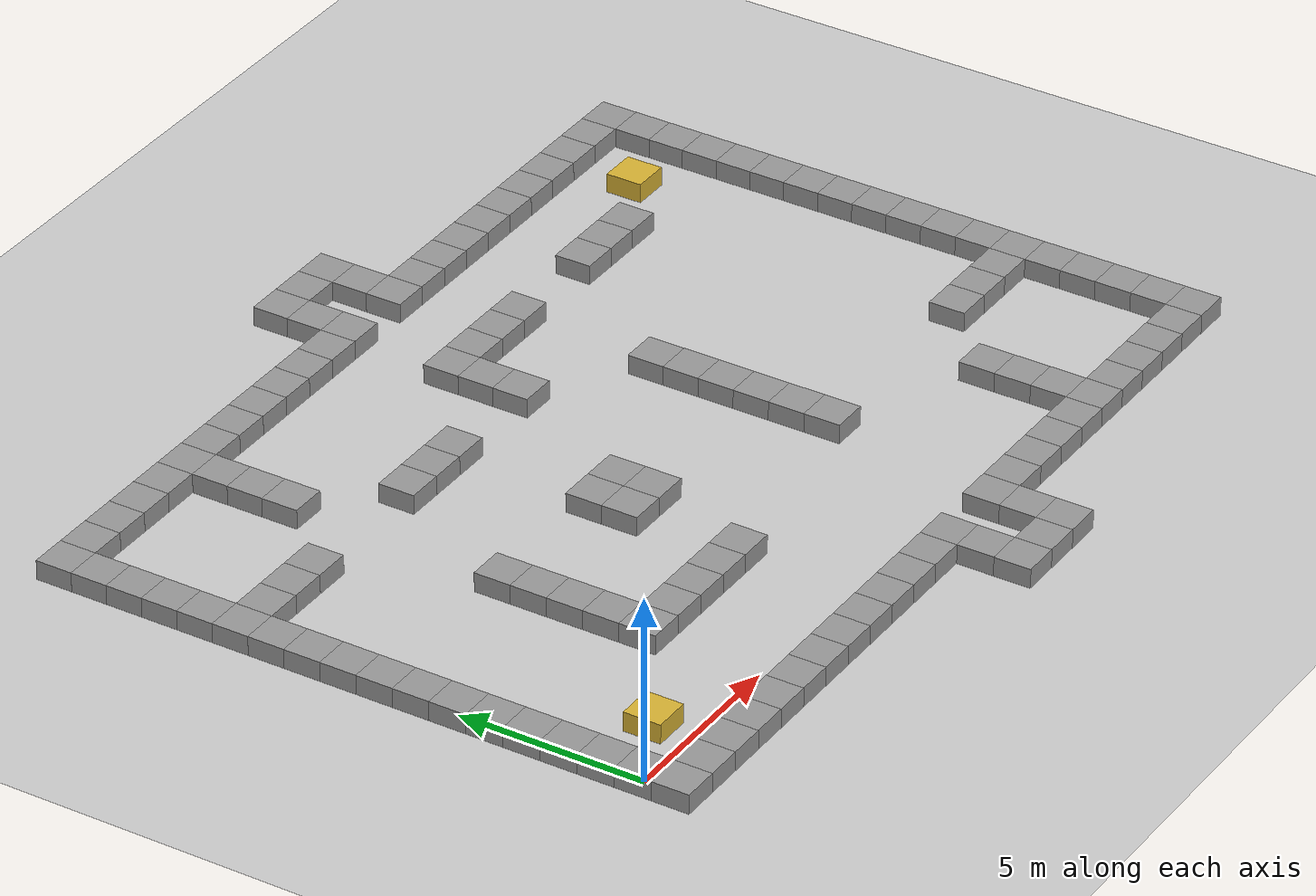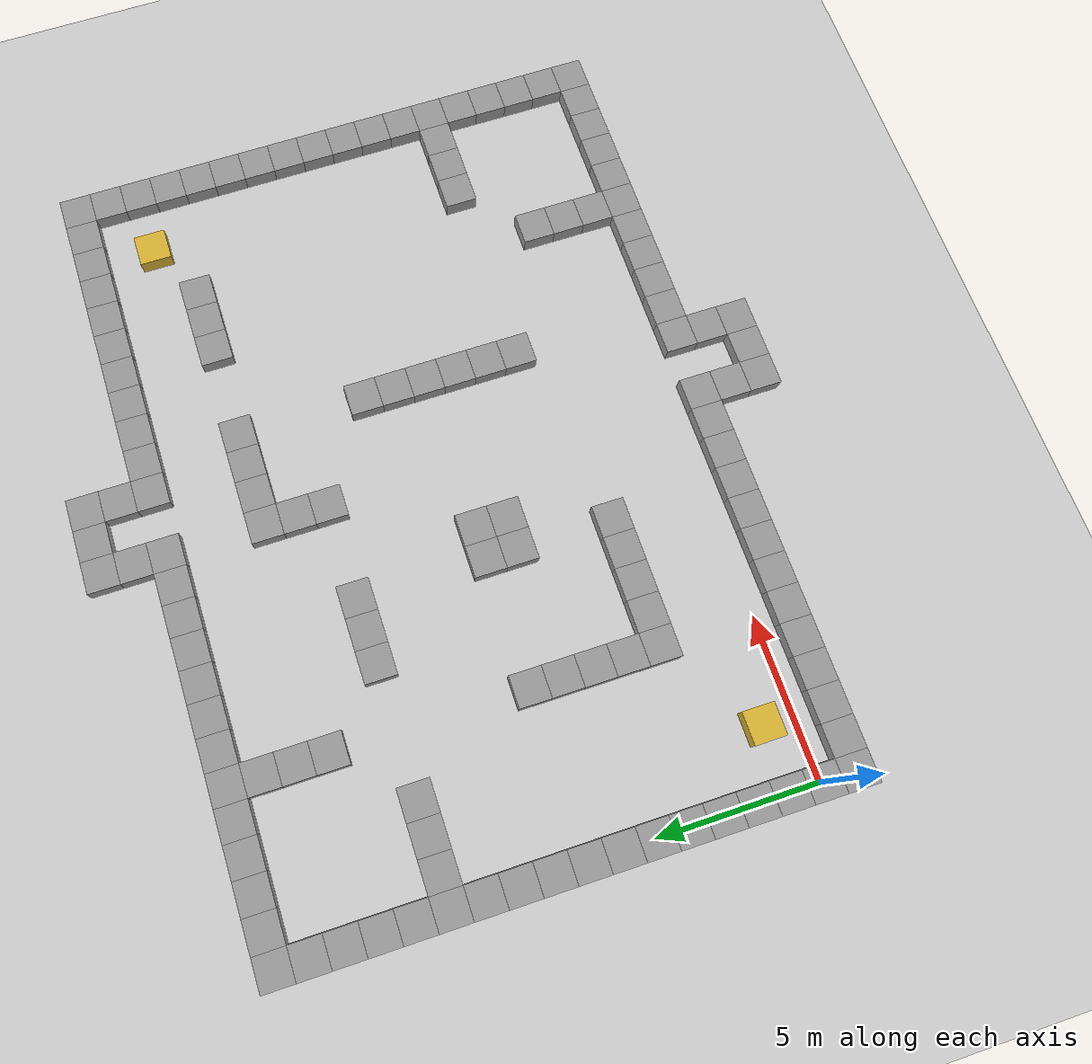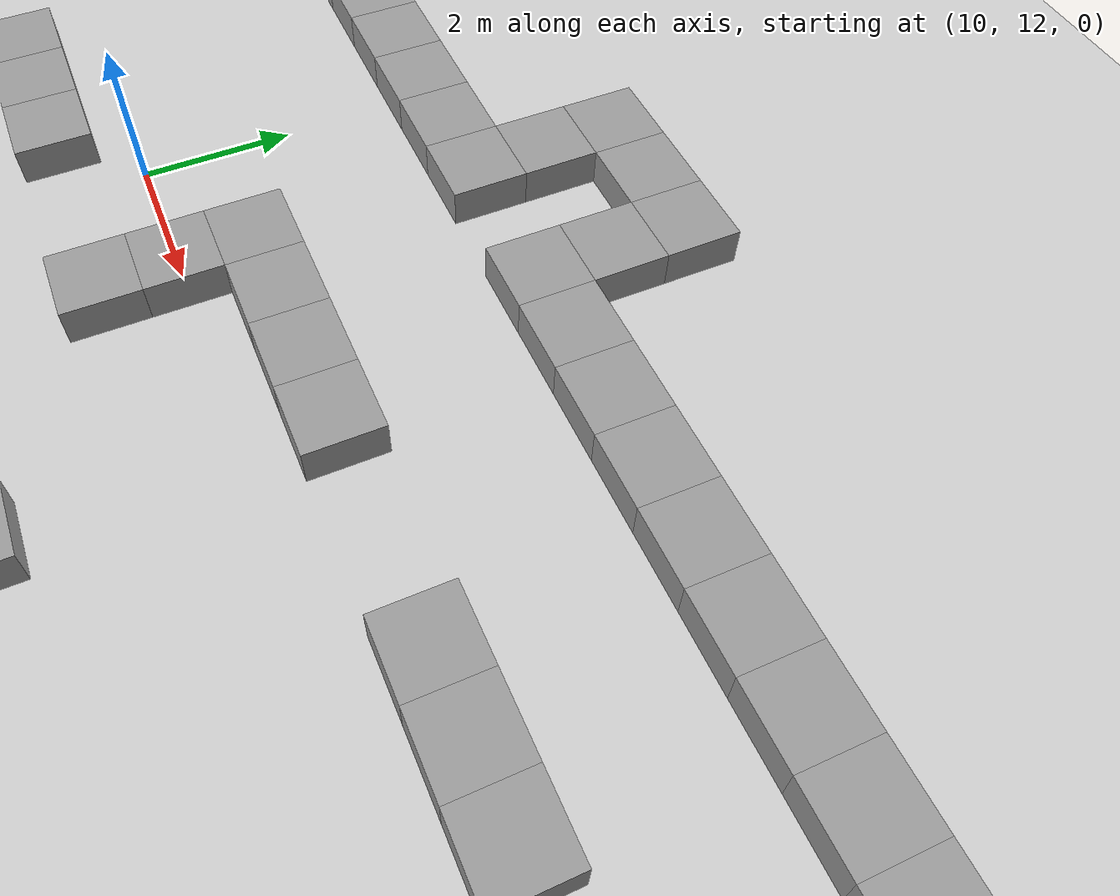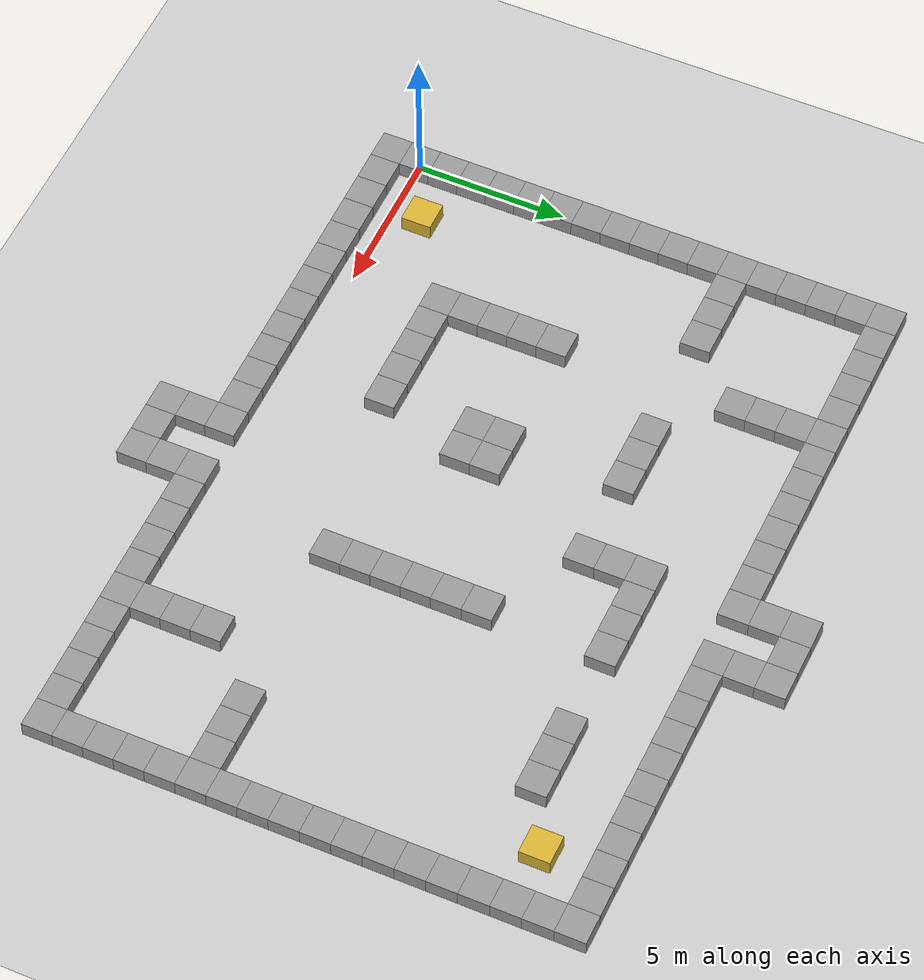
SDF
<sdf version="1.4">
 <world name="default">
  <light name="sun" type="directional">
   <pose>0 0 10 0 -0 0</pose>
   <diffuse>0.8 0.8 0.8 1</diffuse>
   <specular>0.2 0.2 0.2 1</specular>
   <attenuation>
    <range>1000</range>
    <constant>0.9</constant>
    <linear>0.01</linear>
    <quadratic>0.001</quadratic>
   </attenuation>
   <direction>-0.5 0.1 -0.9</direction>
  </light>
  <model name="ground_plane">
   <static>1</static>
   <link name="link">
    <collision name="collision">
     <geometry><plane><normal>0 0 1</normal><size>100 100</size></plane></geometry>
     <surface><friction><ode><mu>100</mu><mu2>50</mu2></ode></friction></surface>
    </collision>
    <visual name="visual">
     <cast_shadows>0</cast_shadows>
     <geometry><plane><normal>0 0 1</normal><size>100 100</size></plane></geometry>
     <material>
      <script><uri>file://media/materials/scripts/gazebo.material</uri><name>Gazebo/Grey</name></script>
     </material>
    </visual>
    <velocity_decay><linear>0</linear><angular>0</angular></velocity_decay>
   </link>
  </model>
  <physics type="ode">
   <max_step_size>0.001</max_step_size>
   <real_time_factor>1</real_time_factor>
   <real_time_update_rate>1000</real_time_update_rate>
   <gravity>0 0 -9.8</gravity>
  </physics>
  <scene><ambient>0.4 0.4 0.4 1</ambient><background>0.7 0.7 0.7 1</background><shadows>1</shadows></scene>
  <spherical_coordinates>
   <surface_model>EARTH_WGS84</surface_model>
   <latitude_deg>0</latitude_deg>
   <longitude_deg>0</longitude_deg>
   <elevation>0</elevation>
   <heading_deg>0</heading_deg>
  </spherical_coordinates>
  <model name="unit_box_1">
   <pose>0 -1 0 0 -0 0</pose>
   <link name="link">
    <inertial>
     <mass>1</mass>
     <inertia><ixx>1</ixx><ixy>0</ixy><ixz>0</ixz><iyy>1</iyy><iyz>0</iyz><izz>1</izz></inertia>
    </inertial>
    <collision name="collision"><geometry><box><size>1 1 1</size></box></geometry></collision>
    <visual name="visual">
     <geometry><box><size>1 1 1</size></box></geometry>
     <material>
      <script><uri>file://media/materials/scripts/gazebo.material</uri><name>Gazebo/Grey</name></script>
     </material>
    </visual>
    <velocity_decay><linear>0</linear><angular>0</angular></velocity_decay>
   </link>
   <static>1</static>
  </model>
  <model name="unit_box_2">
   <pose>1 -1 0 0 -0 0</pose>
   <link name="link">
    <inertial>
     <mass>1</mass>
     <inertia><ixx>1</ixx><ixy>0</ixy><ixz>0</ixz><iyy>1</iyy><iyz>0</iyz><izz>1</izz></inertia>
    </inertial>
    <collision name="collision"><geometry><box><size>1 1 1</size></box></geometry></collision>
    <visual name="visual">
     <geometry><box><size>1 1 1</size></box></geometry>
     <material>
      <script><uri>file://media/materials/scripts/gazebo.material</uri><name>Gazebo/Grey</name></script>
     </material>
    </visual>
    <velocity_decay><linear>0</linear><angular>0</angular></velocity_decay>
   </link>
   <static>1</static>
  </model>
  <model name="unit_box_3">
   <pose>2 -1 0 0 -0 0</pose>
   <link name="link">
    <inertial>
     <mass>1</mass>
     <inertia><ixx>1</ixx><ixy>0</ixy><ixz>0</ixz><iyy>1</iyy><iyz>0</iyz><izz>1</izz></inertia>
    </inertial>
    <collision name="collision"><geometry><box><size>1 1 1</size></box></geometry></collision>
    <visual name="visual">
     <geometry><box><size>1 1 1</size></box></geometry>
     <material>
      <script><uri>file://media/materials/scripts/gazebo.material</uri><name>Gazebo/Grey</name></script>
     </material>
    </visual>
    <velocity_decay><linear>0</linear><angular>0</angular></velocity_decay>
   </link>
   <static>1</static>
  </model>
  <model name="unit_box_4">
   <pose>3 -1 0 0 -0 0</pose>
   <link name="link">
    <inertial>
     <mass>1</mass>
     <inertia><ixx>1</ixx><ixy>0</ixy><ixz>0</ixz><iyy>1</iyy><iyz>0</iyz><izz>1</izz></inertia>
    </inertial>
    <collision name="collision"><geometry><box><size>1 1 1</size></box></geometry></collision>
    <visual name="visual">
     <geometry><box><size>1 1 1</size></box></geometry>
     <material>
      <script><uri>file://media/materials/scripts/gazebo.material</uri><name>Gazebo/Grey</name></script>
     </material>
    </visual>
    <velocity_decay><linear>0</linear><angular>0</angular></velocity_decay>
   </link>
   <static>1</static>
  </model>
  <model name="unit_box_5">
   <pose>4 -1 0 0 -0 0</pose>
   <link name="link">
    <inertial>
     <mass>1</mass>
     <inertia><ixx>1</ixx><ixy>0</ixy><ixz>0</ixz><iyy>1</iyy><iyz>0</iyz><izz>1</izz></inertia>
    </inertial>
    <collision name="collision"><geometry><box><size>1 1 1</size></box></geometry></collision>
    <visual name="visual">
     <geometry><box><size>1 1 1</size></box></geometry>
     <material>
      <script><uri>file://media/materials/scripts/gazebo.material</uri><name>Gazebo/Grey</name></script>
     </material>
    </visual>
    <velocity_decay><linear>0</linear><angular>0</angular></velocity_decay>
   </link>
   <static>1</static>
  </model>
  <model name="unit_box_6">
   <pose>5 -1 0 0 -0 0</pose>
   <link name="link">
    <inertial>
     <mass>1</mass>
     <inertia><ixx>1</ixx><ixy>0</ixy><ixz>0</ixz><iyy>1</iyy><iyz>0</iyz><izz>1</izz></inertia>
    </inertial>
    <collision name="collision"><geometry><box><size>1 1 1</size></box></geometry></collision>
    <visual name="visual">
     <geometry><box><size>1 1 1</size></box></geometry>
     <material>
      <script><uri>file://media/materials/scripts/gazebo.material</uri><name>Gazebo/Grey</name></script>
     </material>
    </visual>
    <velocity_decay><linear>0</linear><angular>0</angular></velocity_decay>
   </link>
   <static>1</static>
  </model>
  <model name="unit_box_7">
   <pose>6 -1 0 0 -0 0</pose>
   <link name="link">
    <inertial>
     <mass>1</mass>
     <inertia><ixx>1</ixx><ixy>0</ixy><ixz>0</ixz><iyy>1</iyy><iyz>0</iyz><izz>1</izz></inertia>
    </inertial>
    <collision name="collision"><geometry><box><size>1 1 1</size></box></geometry></collision>
    <visual name="visual">
     <geometry><box><size>1 1 1</size></box></geometry>
     <material>
      <script><uri>file://media/materials/scripts/gazebo.material</uri><name>Gazebo/Grey</name></script>
     </material>
    </visual>
    <velocity_decay><linear>0</linear><angular>0</angular></velocity_decay>
   </link>
   <static>1</static>
  </model>
  <model name="unit_box_8">
   <pose>7 -1 0 0 -0 0</pose>
   <link name="link">
    <inertial>
     <mass>1</mass>
     <inertia><ixx>1</ixx><ixy>0</ixy><ixz>0</ixz><iyy>1</iyy><iyz>0</iyz><izz>1</izz></inertia>
    </inertial>
    <collision name="collision"><geometry><box><size>1 1 1</size></box></geometry></collision>
    <visual name="visual">
     <geometry><box><size>1 1 1</size></box></geometry>
     <material>
      <script><uri>file://media/materials/scripts/gazebo.material</uri><name>Gazebo/Grey</name></script>
     </material>
    </visual>
    <velocity_decay><linear>0</linear><angular>0</angular></velocity_decay>
   </link>
   <static>1</static>
  </model>
  <model name="unit_box_9">
   <pose>8 -1 0 0 -0 0</pose>
   <link name="link">
    <inertial>
     <mass>1</mass>
     <inertia><ixx>1</ixx><ixy>0</ixy><ixz>0</ixz><iyy>1</iyy><iyz>0</iyz><izz>1</izz></inertia>
    </inertial>
    <collision name="collision"><geometry><box><size>1 1 1</size></box></geometry></collision>
    <visual name="visual">
     <geometry><box><size>1 1 1</size></box></geometry>
     <material>
      <script><uri>file://media/materials/scripts/gazebo.material</uri><name>Gazebo/Grey</name></script>
     </material>
    </visual>
    <velocity_decay><linear>0</linear><angular>0</angular></velocity_decay>
   </link>
   <static>1</static>
  </model>
  <model name="unit_box_10">
   <pose>9 -1 0 0 -0 0</pose>
   <link name="link">
    <inertial>
     <mass>1</mass>
     <inertia><ixx>1</ixx><ixy>0</ixy><ixz>0</ixz><iyy>1</iyy><iyz>0</iyz><izz>1</izz></inertia>
    </inertial>
    <collision name="collision"><geometry><box><size>1 1 1</size></box></geometry></collision>
    <visual name="visual">
     <geometry><box><size>1 1 1</size></box></geometry>
     <material>
      <script><uri>file://media/materials/scripts/gazebo.material</uri><name>Gazebo/Grey</name></script>
     </material>
    </visual>
    <velocity_decay><linear>0</linear><angular>0</angular></velocity_decay>
   </link>
   <static>1</static>
  </model>
  <model name="unit_box_11">
   <pose>10 -1 0 0 -0 0</pose>
   <link name="link">
    <inertial>
     <mass>1</mass>
     <inertia><ixx>1</ixx><ixy>0</ixy><ixz>0</ixz><iyy>1</iyy><iyz>0</iyz><izz>1</izz></inertia>
    </inertial>
    <collision name="collision"><geometry><box><size>1 1 1</size></box></geometry></collision>
    <visual name="visual">
     <geometry><box><size>1 1 1</size></box></geometry>
     <material>
      <script><uri>file://media/materials/scripts/gazebo.material</uri><name>Gazebo/Grey</name></script>
     </material>
    </visual>
    <velocity_decay><linear>0</linear><angular>0</angular></velocity_decay>
   </link>
   <static>1</static>
  </model>
  <model name="unit_box_12">
   <pose>11 -1 0 0 -0 0</pose>
   <link name="link">
    <inertial>
     <mass>1</mass>
     <inertia><ixx>1</ixx><ixy>0</ixy><ixz>0</ixz><iyy>1</iyy><iyz>0</iyz><izz>1</izz></inertia>
    </inertial>
    <collision name="collision"><geometry><box><size>1 1 1</size></box></geometry></collision>
    <visual name="visual">
     <geometry><box><size>1 1 1</size></box></geometry>
     <material>
      <script><uri>file://media/materials/scripts/gazebo.material</uri><name>Gazebo/Grey</name></script>
     </material>
    </visual>
    <velocity_decay><linear>0</linear><angular>0</angular></velocity_decay>
   </link>
   <static>1</static>
  </model>
  <model name="unit_box_13">
   <link name="link">
    <inertial>
     <mass>1</mass>
     <inertia><ixx>1</ixx><ixy>0</ixy><ixz>0</ixz><iyy>1</iyy><iyz>0</iyz><izz>1</izz></inertia>
    </inertial>
    <collision name="collision"><geometry><box><size>1 1 1</size></box></geometry></collision>
    <visual name="visual">
     <geometry><box><size>1 1 1</size></box></geometry>
     <material>
      <script><uri>file://media/materials/scripts/gazebo.material</uri><name>Gazebo/Grey</name></script>
     </material>
    </visual>
    <velocity_decay><linear>0</linear><angular>0</angular></velocity_decay>
   </link>
   <static>1</static>
  </model>
  <model name="unit_box_14">
   <pose>0 1 0 0 -0 0</pose>
   <link name="link">
    <inertial>
     <mass>1</mass>
     <inertia><ixx>1</ixx><ixy>0</ixy><ixz>0</ixz><iyy>1</iyy><iyz>0</iyz><izz>1</izz></inertia>
    </inertial>
    <collision name="collision"><geometry><box><size>1 1 1</size></box></geometry></collision>
    <visual name="visual">
     <geometry><box><size>1 1 1</size></box></geometry>
     <material>
      <script><uri>file://media/materials/scripts/gazebo.material</uri><name>Gazebo/Grey</name></script>
     </material>
    </visual>
    <velocity_decay><linear>0</linear><angular>0</angular></velocity_decay>
   </link>
   <static>1</static>
  </model>
  <model name="unit_box_15">
   <pose>0 2 0 0 -0 0</pose>
   <link name="link">
    <inertial>
     <mass>1</mass>
     <inertia><ixx>1</ixx><ixy>0</ixy><ixz>0</ixz><iyy>1</iyy><iyz>0</iyz><izz>1</izz></inertia>
    </inertial>
    <collision name="collision"><geometry><box><size>1 1 1</size></box></geometry></collision>
    <visual name="visual">
     <geometry><box><size>1 1 1</size></box></geometry>
     <material>
      <script><uri>file://media/materials/scripts/gazebo.material</uri><name>Gazebo/Grey</name></script>
     </material>
    </visual>
    <velocity_decay><linear>0</linear><angular>0</angular></velocity_decay>
   </link>
   <static>1</static>
  </model>
  <model name="unit_box_16">
   <pose>0 3 0 0 -0 0</pose>
   <link name="link">
    <inertial>
     <mass>1</mass>
     <inertia><ixx>1</ixx><ixy>0</ixy><ixz>0</ixz><iyy>1</iyy><iyz>0</iyz><izz>1</izz></inertia>
    </inertial>
    <collision name="collision"><geometry><box><size>1 1 1</size></box></geometry></collision>
    <visual name="visual">
     <geometry><box><size>1 1 1</size></box></geometry>
     <material>
      <script><uri>file://media/materials/scripts/gazebo.material</uri><name>Gazebo/Grey</name></script>
     </material>
    </visual>
    <velocity_decay><linear>0</linear><angular>0</angular></velocity_decay>
   </link>
   <static>1</static>
  </model>
  <model name="unit_box_17">
   <pose>0 4 0 0 -0 0</pose>
   <link name="link">
    <inertial>
     <mass>1</mass>
     <inertia><ixx>1</ixx><ixy>0</ixy><ixz>0</ixz><iyy>1</iyy><iyz>0</iyz><izz>1</izz></inertia>
    </inertial>
    <collision name="collision"><geometry><box><size>1 1 1</size></box></geometry></collision>
    <visual name="visual">
     <geometry><box><size>1 1 1</size></box></geometry>
     <material>
      <script><uri>file://media/materials/scripts/gazebo.material</uri><name>Gazebo/Grey</name></script>
     </material>
    </visual>
    <velocity_decay><linear>0</linear><angular>0</angular></velocity_decay>
   </link>
   <static>1</static>
  </model>
  <model name="unit_box_18">
   <pose>0 5 0 0 -0 0</pose>
   <link name="link">
    <inertial>
     <mass>1</mass>
     <inertia><ixx>1</ixx><ixy>0</ixy><ixz>0</ixz><iyy>1</iyy><iyz>0</iyz><izz>1</izz></inertia>
    </inertial>
    <collision name="collision"><geometry><box><size>1 1 1</size></box></geometry></collision>
    <visual name="visual">
     <geometry><box><size>1 1 1</size></box></geometry>
     <material>
      <script><uri>file://media/materials/scripts/gazebo.material</uri><name>Gazebo/Grey</name></script>
     </material>
    </visual>
    <velocity_decay><linear>0</linear><angular>0</angular></velocity_decay>
   </link>
   <static>1</static>
  </model>
  <model name="unit_box_19">
   <pose>0 6 0 0 -0 0</pose>
   <link name="link">
    <inertial>
     <mass>1</mass>
     <inertia><ixx>1</ixx><ixy>0</ixy><ixz>0</ixz><iyy>1</iyy><iyz>0</iyz><izz>1</izz></inertia>
    </inertial>
    <collision name="collision"><geometry><box><size>1 1 1</size></box></geometry></collision>
    <visual name="visual">
     <geometry><box><size>1 1 1</size></box></geometry>
     <material>
      <script><uri>file://media/materials/scripts/gazebo.material</uri><name>Gazebo/Grey</name></script>
     </material>
    </visual>
    <velocity_decay><linear>0</linear><angular>0</angular></velocity_decay>
   </link>
   <static>1</static>
  </model>
  <model name="unit_box_20">
   <pose>0 7 0 0 -0 0</pose>
   <link name="link">
    <inertial>
     <mass>1</mass>
     <inertia><ixx>1</ixx><ixy>0</ixy><ixz>0</ixz><iyy>1</iyy><iyz>0</iyz><izz>1</izz></inertia>
    </inertial>
    <collision name="collision"><geometry><box><size>1 1 1</size></box></geometry></collision>
    <visual name="visual">
     <geometry><box><size>1 1 1</size></box></geometry>
     <material>
      <script><uri>file://media/materials/scripts/gazebo.material</uri><name>Gazebo/Grey</name></script>
     </material>
    </visual>
    <velocity_decay><linear>0</linear><angular>0</angular></velocity_decay>
   </link>
   <static>1</static>
  </model>
  <model name="unit_box_21">
   <pose>0 8 0 0 -0 0</pose>
   <link name="link">
    <inertial>
     <mass>1</mass>
     <inertia><ixx>1</ixx><ixy>0</ixy><ixz>0</ixz><iyy>1</iyy><iyz>0</iyz><izz>1</izz></inertia>
    </inertial>
    <collision name="collision"><geometry><box><size>1 1 1</size></box></geometry></collision>
    <visual name="visual">
     <geometry><box><size>1 1 1</size></box></geometry>
     <material>
      <script><uri>file://media/materials/scripts/gazebo.material</uri><name>Gazebo/Grey</name></script>
     </material>
    </visual>
    <velocity_decay><linear>0</linear><angular>0</angular></velocity_decay>
   </link>
   <static>1</static>
  </model>
  <model name="unit_box_22">
   <pose>0 9 0 0 -0 0</pose>
   <link name="link">
    <inertial>
     <mass>1</mass>
     <inertia><ixx>1</ixx><ixy>0</ixy><ixz>0</ixz><iyy>1</iyy><iyz>0</iyz><izz>1</izz></inertia>
    </inertial>
    <collision name="collision"><geometry><box><size>1 1 1</size></box></geometry></collision>
    <visual name="visual">
     <geometry><box><size>1 1 1</size></box></geometry>
     <material>
      <script><uri>file://media/materials/scripts/gazebo.material</uri><name>Gazebo/Grey</name></script>
     </material>
    </visual>
    <velocity_decay><linear>0</linear><angular>0</angular></velocity_decay>
   </link>
   <static>1</static>
  </model>
  <model name="unit_box_23">
   <pose>0 10 0 0 -0 0</pose>
   <link name="link">
    <inertial>
     <mass>1</mass>
     <inertia><ixx>1</ixx><ixy>0</ixy><ixz>0</ixz><iyy>1</iyy><iyz>0</iyz><izz>1</izz></inertia>
    </inertial>
    <collision name="collision"><geometry><box><size>1 1 1</size></box></geometry></collision>
    <visual name="visual">
     <geometry><box><size>1 1 1</size></box></geometry>
     <material>
      <script><uri>file://media/materials/scripts/gazebo.material</uri><name>Gazebo/Grey</name></script>
     </material>
    </visual>
    <velocity_decay><linear>0</linear><angular>0</angular></velocity_decay>
   </link>
   <static>1</static>
  </model>
  <model name="unit_box_24">
   <pose>0 11 0 0 -0 0</pose>
   <link name="link">
    <inertial>
     <mass>1</mass>
     <inertia><ixx>1</ixx><ixy>0</ixy><ixz>0</ixz><iyy>1</iyy><iyz>0</iyz><izz>1</izz></inertia>
    </inertial>
    <collision name="collision"><geometry><box><size>1 1 1</size></box></geometry></collision>
    <visual name="visual">
     <geometry><box><size>1 1 1</size></box></geometry>
     <material>
      <script><uri>file://media/materials/scripts/gazebo.material</uri><name>Gazebo/Grey</name></script>
     </material>
    </visual>
    <velocity_decay><linear>0</linear><angular>0</angular></velocity_decay>
   </link>
   <static>1</static>
  </model>
  <model name="unit_box_25">
   <pose>0 12 0 0 -0 0</pose>
   <link name="link">
    <inertial>
     <mass>1</mass>
     <inertia><ixx>1</ixx><ixy>0</ixy><ixz>0</ixz><iyy>1</iyy><iyz>0</iyz><izz>1</izz></inertia>
    </inertial>
    <collision name="collision"><geometry><box><size>1 1 1</size></box></geometry></collision>
    <visual name="visual">
     <geometry><box><size>1 1 1</size></box></geometry>
     <material>
      <script><uri>file://media/materials/scripts/gazebo.material</uri><name>Gazebo/Grey</name></script>
     </material>
    </visual>
    <velocity_decay><linear>0</linear><angular>0</angular></velocity_decay>
   </link>
   <static>1</static>
  </model>
  <model name="unit_box_26">
   <pose>0 13 0 0 -0 0</pose>
   <link name="link">
    <inertial>
     <mass>1</mass>
     <inertia><ixx>1</ixx><ixy>0</ixy><ixz>0</ixz><iyy>1</iyy><iyz>0</iyz><izz>1</izz></inertia>
    </inertial>
    <collision name="collision"><geometry><box><size>1 1 1</size></box></geometry></collision>
    <visual name="visual">
     <geometry><box><size>1 1 1</size></box></geometry>
     <material>
      <script><uri>file://media/materials/scripts/gazebo.material</uri><name>Gazebo/Grey</name></script>
     </material>
    </visual>
    <velocity_decay><linear>0</linear><angular>0</angular></velocity_decay>
   </link>
   <static>1</static>
  </model>
  <model name="unit_box_27">
   <pose>0 14 0 0 -0 0</pose>
   <link name="link">
    <inertial>
     <mass>1</mass>
     <inertia><ixx>1</ixx><ixy>0</ixy><ixz>0</ixz><iyy>1</iyy><iyz>0</iyz><izz>1</izz></inertia>
    </inertial>
    <collision name="collision"><geometry><box><size>1 1 1</size></box></geometry></collision>
    <visual name="visual">
     <geometry><box><size>1 1 1</size></box></geometry>
     <material>
      <script><uri>file://media/materials/scripts/gazebo.material</uri><name>Gazebo/Grey</name></script>
     </material>
    </visual>
    <velocity_decay><linear>0</linear><angular>0</angular></velocity_decay>
   </link>
   <static>1</static>
  </model>
  <model name="unit_box_28">
   <pose>0 15 0 0 -0 0</pose>
   <link name="link">
    <inertial>
     <mass>1</mass>
     <inertia><ixx>1</ixx><ixy>0</ixy><ixz>0</ixz><iyy>1</iyy><iyz>0</iyz><izz>1</izz></inertia>
    </inertial>
    <collision name="collision"><geometry><box><size>1 1 1</size></box></geometry></collision>
    <visual name="visual">
     <geometry><box><size>1 1 1</size></box></geometry>
     <material>
      <script><uri>file://media/materials/scripts/gazebo.material</uri><name>Gazebo/Grey</name></script>
     </material>
    </visual>
    <velocity_decay><linear>0</linear><angular>0</angular></velocity_decay>
   </link>
   <static>1</static>
  </model>
  <model name="unit_box_29">
   <pose>0 16 0 0 -0 0</pose>
   <link name="link">
    <inertial>
     <mass>1</mass>
     <inertia><ixx>1</ixx><ixy>0</ixy><ixz>0</ixz><iyy>1</iyy><iyz>0</iyz><izz>1</izz></inertia>
    </inertial>
    <collision name="collision"><geometry><box><size>1 1 1</size></box></geometry></collision>
    <visual name="visual">
     <geometry><box><size>1 1 1</size></box></geometry>
     <material>
      <script><uri>file://media/materials/scripts/gazebo.material</uri><name>Gazebo/Grey</name></script>
     </material>
    </visual>
    <velocity_decay><linear>0</linear><angular>0</angular></velocity_decay>
   </link>
   <static>1</static>
  </model>
  <model name="unit_box_30">
   <pose>1 16 0 0 -0 0</pose>
   <link name="link">
    <inertial>
     <mass>1</mass>
     <inertia><ixx>1</ixx><ixy>0</ixy><ixz>0</ixz><iyy>1</iyy><iyz>0</iyz><izz>1</izz></inertia>
    </inertial>
    <collision name="collision"><geometry><box><size>1 1 1</size></box></geometry></collision>
    <visual name="visual">
     <geometry><box><size>1 1 1</size></box></geometry>
     <material>
      <script><uri>file://media/materials/scripts/gazebo.material</uri><name>Gazebo/Grey</name></script>
     </material>
    </visual>
    <velocity_decay><linear>0</linear><angular>0</angular></velocity_decay>
   </link>
   <static>1</static>
  </model>
  <model name="unit_box_31">
   <pose>2 16 0 0 -0 0</pose>
   <link name="link">
    <inertial>
     <mass>1</mass>
     <inertia><ixx>1</ixx><ixy>0</ixy><ixz>0</ixz><iyy>1</iyy><iyz>0</iyz><izz>1</izz></inertia>
    </inertial>
    <collision name="collision"><geometry><box><size>1 1 1</size></box></geometry></collision>
    <visual name="visual">
     <geometry><box><size>1 1 1</size></box></geometry>
     <material>
      <script><uri>file://media/materials/scripts/gazebo.material</uri><name>Gazebo/Grey</name></script>
     </material>
    </visual>
    <velocity_decay><linear>0</linear><angular>0</angular></velocity_decay>
   </link>
   <static>1</static>
  </model>
  <model name="unit_box_32">
   <pose>3 16 0 0 -0 0</pose>
   <link name="link">
    <inertial>
     <mass>1</mass>
     <inertia><ixx>1</ixx><ixy>0</ixy><ixz>0</ixz><iyy>1</iyy><iyz>0</iyz><izz>1</izz></inertia>
    </inertial>
    <collision name="collision"><geometry><box><size>1 1 1</size></box></geometry></collision>
    <visual name="visual">
     <geometry><box><size>1 1 1</size></box></geometry>
     <material>
      <script><uri>file://media/materials/scripts/gazebo.material</uri><name>Gazebo/Grey</name></script>
     </material>
    </visual>
    <velocity_decay><linear>0</linear><angular>0</angular></velocity_decay>
   </link>
   <static>1</static>
  </model>
  <model name="unit_box_33">
   <pose>4 16 0 0 -0 0</pose>
   <link name="link">
    <inertial>
     <mass>1</mass>
     <inertia><ixx>1</ixx><ixy>0</ixy><ixz>0</ixz><iyy>1</iyy><iyz>0</iyz><izz>1</izz></inertia>
    </inertial>
    <collision name="collision"><geometry><box><size>1 1 1</size></box></geometry></collision>
    <visual name="visual">
     <geometry><box><size>1 1 1</size></box></geometry>
     <material>
      <script><uri>file://media/materials/scripts/gazebo.material</uri><name>Gazebo/Grey</name></script>
     </material>
    </visual>
    <velocity_decay><linear>0</linear><angular>0</angular></velocity_decay>
   </link>
   <static>1</static>
  </model>
  <model name="unit_box_34">
   <pose>5 16 0 0 -0 0</pose>
   <link name="link">
    <inertial>
     <mass>1</mass>
     <inertia><ixx>1</ixx><ixy>0</ixy><ixz>0</ixz><iyy>1</iyy><iyz>0</iyz><izz>1</izz></inertia>
    </inertial>
    <collision name="collision"><geometry><box><size>1 1 1</size></box></geometry></collision>
    <visual name="visual">
     <geometry><box><size>1 1 1</size></box></geometry>
     <material>
      <script><uri>file://media/materials/scripts/gazebo.material</uri><name>Gazebo/Grey</name></script>
     </material>
    </visual>
    <velocity_decay><linear>0</linear><angular>0</angular></velocity_decay>
   </link>
   <static>1</static>
  </model>
  <model name="unit_box_35">
   <pose>6 16 0 0 -0 0</pose>
   <link name="link">
    <inertial>
     <mass>1</mass>
     <inertia><ixx>1</ixx><ixy>0</ixy><ixz>0</ixz><iyy>1</iyy><iyz>0</iyz><izz>1</izz></inertia>
    </inertial>
    <collision name="collision"><geometry><box><size>1 1 1</size></box></geometry></collision>
    <visual name="visual">
     <geometry><box><size>1 1 1</size></box></geometry>
     <material>
      <script><uri>file://media/materials/scripts/gazebo.material</uri><name>Gazebo/Grey</name></script>
     </material>
    </visual>
    <velocity_decay><linear>0</linear><angular>0</angular></velocity_decay>
   </link>
   <static>1</static>
  </model>
  <model name="unit_box_36">
   <pose>7 16 0 0 -0 0</pose>
   <link name="link">
    <inertial>
     <mass>1</mass>
     <inertia><ixx>1</ixx><ixy>0</ixy><ixz>0</ixz><iyy>1</iyy><iyz>0</iyz><izz>1</izz></inertia>
    </inertial>
    <collision name="collision"><geometry><box><size>1 1 1</size></box></geometry></collision>
    <visual name="visual">
     <geometry><box><size>1 1 1</size></box></geometry>
     <material>
      <script><uri>file://media/materials/scripts/gazebo.material</uri><name>Gazebo/Grey</name></script>
     </material>
    </visual>
    <velocity_decay><linear>0</linear><angular>0</angular></velocity_decay>
   </link>
   <static>1</static>
  </model>
  <model name="unit_box_37">
   <pose>8 16 0 0 -0 0</pose>
   <link name="link">
    <inertial>
     <mass>1</mass>
     <inertia><ixx>1</ixx><ixy>0</ixy><ixz>0</ixz><iyy>1</iyy><iyz>0</iyz><izz>1</izz></inertia>
    </inertial>
    <collision name="collision"><geometry><box><size>1 1 1</size></box></geometry></collision>
    <visual name="visual">
     <geometry><box><size>1 1 1</size></box></geometry>
     <material>
      <script><uri>file://media/materials/scripts/gazebo.material</uri><name>Gazebo/Grey</name></script>
     </material>
    </visual>
    <velocity_decay><linear>0</linear><angular>0</angular></velocity_decay>
   </link>
   <static>1</static>
  </model>
  <model name="unit_box_38">
   <pose>9 16 0 0 -0 0</pose>
   <link name="link">
    <inertial>
     <mass>1</mass>
     <inertia><ixx>1</ixx><ixy>0</ixy><ixz>0</ixz><iyy>1</iyy><iyz>0</iyz><izz>1</izz></inertia>
    </inertial>
    <collision name="collision"><geometry><box><size>1 1 1</size></box></geometry></collision>
    <visual name="visual">
     <geometry><box><size>1 1 1</size></box></geometry>
     <material>
      <script><uri>file://media/materials/scripts/gazebo.material</uri><name>Gazebo/Grey</name></script>
     </material>
    </visual>
    <velocity_decay><linear>0</linear><angular>0</angular></velocity_decay>
   </link>
   <static>1</static>
  </model>
  <model name="unit_box_39">
   <pose>10 16 0 0 -0 0</pose>
   <link name="link">
    <inertial>
     <mass>1</mass>
     <inertia><ixx>1</ixx><ixy>0</ixy><ixz>0</ixz><iyy>1</iyy><iyz>0</iyz><izz>1</izz></inertia>
    </inertial>
    <collision name="collision"><geometry><box><size>1 1 1</size></box></geometry></collision>
    <visual name="visual">
     <geometry><box><size>1 1 1</size></box></geometry>
     <material>
      <script><uri>file://media/materials/scripts/gazebo.material</uri><name>Gazebo/Grey</name></script>
     </material>
    </visual>
    <velocity_decay><linear>0</linear><angular>0</angular></velocity_decay>
   </link>
   <static>1</static>
  </model>
  <model name="unit_box_40">
   <pose>11 16 0 0 -0 0</pose>
   <link name="link">
    <inertial>
     <mass>1</mass>
     <inertia><ixx>1</ixx><ixy>0</ixy><ixz>0</ixz><iyy>1</iyy><iyz>0</iyz><izz>1</izz></inertia>
    </inertial>
    <collision name="collision"><geometry><box><size>1 1 1</size></box></geometry></collision>
    <visual name="visual">
     <geometry><box><size>1 1 1</size></box></geometry>
     <material>
      <script><uri>file://media/materials/scripts/gazebo.material</uri><name>Gazebo/Grey</name></script>
     </material>
    </visual>
    <velocity_decay><linear>0</linear><angular>0</angular></velocity_decay>
   </link>
   <static>1</static>
  </model>
  <model name="unit_box_41">
   <pose>12 16 0 0 -0 0</pose>
   <link name="link">
    <inertial>
     <mass>1</mass>
     <inertia><ixx>1</ixx><ixy>0</ixy><ixz>0</ixz><iyy>1</iyy><iyz>0</iyz><izz>1</izz></inertia>
    </inertial>
    <collision name="collision"><geometry><box><size>1 1 1</size></box></geometry></collision>
    <visual name="visual">
     <geometry><box><size>1 1 1</size></box></geometry>
     <material>
      <script><uri>file://media/materials/scripts/gazebo.material</uri><name>Gazebo/Grey</name></script>
     </material>
    </visual>
    <velocity_decay><linear>0</linear><angular>0</angular></velocity_decay>
   </link>
   <static>1</static>
  </model>
  <model name="unit_box_42">
   <pose>14 16 0 0 -0 0</pose>
   <link name="link">
    <inertial>
     <mass>1</mass>
     <inertia><ixx>1</ixx><ixy>0</ixy><ixz>0</ixz><iyy>1</iyy><iyz>0</iyz><izz>1</izz></inertia>
    </inertial>
    <collision name="collision"><geometry><box><size>1 1 1</size></box></geometry></collision>
    <visual name="visual">
     <geometry><box><size>1 1 1</size></box></geometry>
     <material>
      <script><uri>file://media/materials/scripts/gazebo.material</uri><name>Gazebo/Grey</name></script>
     </material>
    </visual>
    <velocity_decay><linear>0</linear><angular>0</angular></velocity_decay>
   </link>
   <static>1</static>
  </model>
  <model name="unit_box_43">
   <pose>15 16 0 0 -0 0</pose>
   <link name="link">
    <inertial>
     <mass>1</mass>
     <inertia><ixx>1</ixx><ixy>0</ixy><ixz>0</ixz><iyy>1</iyy><iyz>0</iyz><izz>1</izz></inertia>
    </inertial>
    <collision name="collision"><geometry><box><size>1 1 1</size></box></geometry></collision>
    <visual name="visual">
     <geometry><box><size>1 1 1</size></box></geometry>
     <material>
      <script><uri>file://media/materials/scripts/gazebo.material</uri><name>Gazebo/Grey</name></script>
     </material>
    </visual>
    <velocity_decay><linear>0</linear><angular>0</angular></velocity_decay>
   </link>
   <static>1</static>
  </model>
  <model name="unit_box_44">
   <pose>16 16 0 0 -0 0</pose>
   <link name="link">
    <inertial>
     <mass>1</mass>
     <inertia><ixx>1</ixx><ixy>0</ixy><ixz>0</ixz><iyy>1</iyy><iyz>0</iyz><izz>1</izz></inertia>
    </inertial>
    <collision name="collision"><geometry><box><size>1 1 1</size></box></geometry></collision>
    <visual name="visual">
     <geometry><box><size>1 1 1</size></box></geometry>
     <material>
      <script><uri>file://media/materials/scripts/gazebo.material</uri><name>Gazebo/Grey</name></script>
     </material>
    </visual>
    <velocity_decay><linear>0</linear><angular>0</angular></velocity_decay>
   </link>
   <static>1</static>
  </model>
  <model name="unit_box_45">
   <pose>17 16 0 0 -0 0</pose>
   <link name="link">
    <inertial>
     <mass>1</mass>
     <inertia><ixx>1</ixx><ixy>0</ixy><ixz>0</ixz><iyy>1</iyy><iyz>0</iyz><izz>1</izz></inertia>
    </inertial>
    <collision name="collision"><geometry><box><size>1 1 1</size></box></geometry></collision>
    <visual name="visual">
     <geometry><box><size>1 1 1</size></box></geometry>
     <material>
      <script><uri>file://media/materials/scripts/gazebo.material</uri><name>Gazebo/Grey</name></script>
     </material>
    </visual>
    <velocity_decay><linear>0</linear><angular>0</angular></velocity_decay>
   </link>
   <static>1</static>
  </model>
  <model name="unit_box_46">
   <pose>18 16 0 0 -0 0</pose>
   <link name="link">
    <inertial>
     <mass>1</mass>
     <inertia><ixx>1</ixx><ixy>0</ixy><ixz>0</ixz><iyy>1</iyy><iyz>0</iyz><izz>1</izz></inertia>
    </inertial>
    <collision name="collision"><geometry><box><size>1 1 1</size></box></geometry></collision>
    <visual name="visual">
     <geometry><box><size>1 1 1</size></box></geometry>
     <material>
      <script><uri>file://media/materials/scripts/gazebo.material</uri><name>Gazebo/Grey</name></script>
     </material>
    </visual>
    <velocity_decay><linear>0</linear><angular>0</angular></velocity_decay>
   </link>
   <static>1</static>
  </model>
  <model name="unit_box_47">
   <pose>19 16 0 0 -0 0</pose>
   <link name="link">
    <inertial>
     <mass>1</mass>
     <inertia><ixx>1</ixx><ixy>0</ixy><ixz>0</ixz><iyy>1</iyy><iyz>0</iyz><izz>1</izz></inertia>
    </inertial>
    <collision name="collision"><geometry><box><size>1 1 1</size></box></geometry></collision>
    <visual name="visual">
     <geometry><box><size>1 1 1</size></box></geometry>
     <material>
      <script><uri>file://media/materials/scripts/gazebo.material</uri><name>Gazebo/Grey</name></script>
     </material>
    </visual>
    <velocity_decay><linear>0</linear><angular>0</angular></velocity_decay>
   </link>
   <static>1</static>
  </model>
  <model name="unit_box_48">
   <pose>20 16 0 0 -0 0</pose>
   <link name="link">
    <inertial>
     <mass>1</mass>
     <inertia><ixx>1</ixx><ixy>0</ixy><ixz>0</ixz><iyy>1</iyy><iyz>0</iyz><izz>1</izz></inertia>
    </inertial>
    <collision name="collision"><geometry><box><size>1 1 1</size></box></geometry></collision>
    <visual name="visual">
     <geometry><box><size>1 1 1</size></box></geometry>
     <material>
      <script><uri>file://media/materials/scripts/gazebo.material</uri><name>Gazebo/Grey</name></script>
     </material>
    </visual>
    <velocity_decay><linear>0</linear><angular>0</angular></velocity_decay>
   </link>
   <static>1</static>
  </model>
  <model name="unit_box_49">
   <pose>21 16 0 0 -0 0</pose>
   <link name="link">
    <inertial>
     <mass>1</mass>
     <inertia><ixx>1</ixx><ixy>0</ixy><ixz>0</ixz><iyy>1</iyy><iyz>0</iyz><izz>1</izz></inertia>
    </inertial>
    <collision name="collision"><geometry><box><size>1 1 1</size></box></geometry></collision>
    <visual name="visual">
     <geometry><box><size>1 1 1</size></box></geometry>
     <material>
      <script><uri>file://media/materials/scripts/gazebo.material</uri><name>Gazebo/Grey</name></script>
     </material>
    </visual>
    <velocity_decay><linear>0</linear><angular>0</angular></velocity_decay>
   </link>
   <static>1</static>
  </model>
  <model name="unit_box_50">
   <pose>22 16 0 0 -0 0</pose>
   <link name="link">
    <inertial>
     <mass>1</mass>
     <inertia><ixx>1</ixx><ixy>0</ixy><ixz>0</ixz><iyy>1</iyy><iyz>0</iyz><izz>1</izz></inertia>
    </inertial>
    <collision name="collision"><geometry><box><size>1 1 1</size></box></geometry></collision>
    <visual name="visual">
     <geometry><box><size>1 1 1</size></box></geometry>
     <material>
      <script><uri>file://media/materials/scripts/gazebo.material</uri><name>Gazebo/Grey</name></script>
     </material>
    </visual>
    <velocity_decay><linear>0</linear><angular>0</angular></velocity_decay>
   </link>
   <static>1</static>
  </model>
  <model name="unit_box_51">
   <pose>23 16 0 0 -0 0</pose>
   <link name="link">
    <inertial>
     <mass>1</mass>
     <inertia><ixx>1</ixx><ixy>0</ixy><ixz>0</ixz><iyy>1</iyy><iyz>0</iyz><izz>1</izz></inertia>
    </inertial>
    <collision name="collision"><geometry><box><size>1 1 1</size></box></geometry></collision>
    <visual name="visual">
     <geometry><box><size>1 1 1</size></box></geometry>
     <material>
      <script><uri>file://media/materials/scripts/gazebo.material</uri><name>Gazebo/Grey</name></script>
     </material>
    </visual>
    <velocity_decay><linear>0</linear><angular>0</angular></velocity_decay>
   </link>
   <static>1</static>
  </model>
  <model name="unit_box_52">
   <pose>24 16 0 0 -0 0</pose>
   <link name="link">
    <inertial>
     <mass>1</mass>
     <inertia><ixx>1</ixx><ixy>0</ixy><ixz>0</ixz><iyy>1</iyy><iyz>0</iyz><izz>1</izz></inertia>
    </inertial>
    <collision name="collision"><geometry><box><size>1 1 1</size></box></geometry></collision>
    <visual name="visual">
     <geometry><box><size>1 1 1</size></box></geometry>
     <material>
      <script><uri>file://media/materials/scripts/gazebo.material</uri><name>Gazebo/Grey</name></script>
     </material>
    </visual>
    <velocity_decay><linear>0</linear><angular>0</angular></velocity_decay>
   </link>
   <static>1</static>
  </model>
  <model name="unit_box_53">
   <pose>24 15 0 0 -0 0</pose>
   <link name="link">
    <inertial>
     <mass>1</mass>
     <inertia><ixx>1</ixx><ixy>0</ixy><ixz>0</ixz><iyy>1</iyy><iyz>0</iyz><izz>1</izz></inertia>
    </inertial>
    <collision name="collision"><geometry><box><size>1 1 1</size></box></geometry></collision>
    <visual name="visual">
     <geometry><box><size>1 1 1</size></box></geometry>
     <material>
      <script><uri>file://media/materials/scripts/gazebo.material</uri><name>Gazebo/Grey</name></script>
     </material>
    </visual>
    <velocity_decay><linear>0</linear><angular>0</angular></velocity_decay>
   </link>
   <static>1</static>
  </model>
  <model name="unit_box_54">
   <pose>24 14 0 0 -0 0</pose>
   <link name="link">
    <inertial>
     <mass>1</mass>
     <inertia><ixx>1</ixx><ixy>0</ixy><ixz>0</ixz><iyy>1</iyy><iyz>0</iyz><izz>1</izz></inertia>
    </inertial>
    <collision name="collision"><geometry><box><size>1 1 1</size></box></geometry></collision>
    <visual name="visual">
     <geometry><box><size>1 1 1</size></box></geometry>
     <material>
      <script><uri>file://media/materials/scripts/gazebo.material</uri><name>Gazebo/Grey</name></script>
     </material>
    </visual>
    <velocity_decay><linear>0</linear><angular>0</angular></velocity_decay>
   </link>
   <static>1</static>
  </model>
  <model name="unit_box_55">
   <pose>24 13 0 0 -0 0</pose>
   <link name="link">
    <inertial>
     <mass>1</mass>
     <inertia><ixx>1</ixx><ixy>0</ixy><ixz>0</ixz><iyy>1</iyy><iyz>0</iyz><izz>1</izz></inertia>
    </inertial>
    <collision name="collision"><geometry><box><size>1 1 1</size></box></geometry></collision>
    <visual name="visual">
     <geometry><box><size>1 1 1</size></box></geometry>
     <material>
      <script><uri>file://media/materials/scripts/gazebo.material</uri><name>Gazebo/Grey</name></script>
     </material>
    </visual>
    <velocity_decay><linear>0</linear><angular>0</angular></velocity_decay>
   </link>
   <static>1</static>
  </model>
  <model name="unit_box_56">
   <pose>24 12 0 0 -0 0</pose>
   <link name="link">
    <inertial>
     <mass>1</mass>
     <inertia><ixx>1</ixx><ixy>0</ixy><ixz>0</ixz><iyy>1</iyy><iyz>0</iyz><izz>1</izz></inertia>
    </inertial>
    <collision name="collision"><geometry><box><size>1 1 1</size></box></geometry></collision>
    <visual name="visual">
     <geometry><box><size>1 1 1</size></box></geometry>
     <material>
      <script><uri>file://media/materials/scripts/gazebo.material</uri><name>Gazebo/Grey</name></script>
     </material>
    </visual>
    <velocity_decay><linear>0</linear><angular>0</angular></velocity_decay>
   </link>
   <static>1</static>
  </model>
  <model name="unit_box_57">
   <pose>24 11 0 0 -0 0</pose>
   <link name="link">
    <inertial>
     <mass>1</mass>
     <inertia><ixx>1</ixx><ixy>0</ixy><ixz>0</ixz><iyy>1</iyy><iyz>0</iyz><izz>1</izz></inertia>
    </inertial>
    <collision name="collision"><geometry><box><size>1 1 1</size></box></geometry></collision>
    <visual name="visual">
     <geometry><box><size>1 1 1</size></box></geometry>
     <material>
      <script><uri>file://media/materials/scripts/gazebo.material</uri><name>Gazebo/Grey</name></script>
     </material>
    </visual>
    <velocity_decay><linear>0</linear><angular>0</angular></velocity_decay>
   </link>
   <static>1</static>
  </model>
  <model name="unit_box_58">
   <pose>24 10 0 0 -0 0</pose>
   <link name="link">
    <inertial>
     <mass>1</mass>
     <inertia><ixx>1</ixx><ixy>0</ixy><ixz>0</ixz><iyy>1</iyy><iyz>0</iyz><izz>1</izz></inertia>
    </inertial>
    <collision name="collision"><geometry><box><size>1 1 1</size></box></geometry></collision>
    <visual name="visual">
     <geometry><box><size>1 1 1</size></box></geometry>
     <material>
      <script><uri>file://media/materials/scripts/gazebo.material</uri><name>Gazebo/Grey</name></script>
     </material>
    </visual>
    <velocity_decay><linear>0</linear><angular>0</angular></velocity_decay>
   </link>
   <static>1</static>
  </model>
  <model name="unit_box_59">
   <pose>24 9 0 0 -0 0</pose>
   <link name="link">
    <inertial>
     <mass>1</mass>
     <inertia><ixx>1</ixx><ixy>0</ixy><ixz>0</ixz><iyy>1</iyy><iyz>0</iyz><izz>1</izz></inertia>
    </inertial>
    <collision name="collision"><geometry><box><size>1 1 1</size></box></geometry></collision>
    <visual name="visual">
     <geometry><box><size>1 1 1</size></box></geometry>
     <material>
      <script><uri>file://media/materials/scripts/gazebo.material</uri><name>Gazebo/Grey</name></script>
     </material>
    </visual>
    <velocity_decay><linear>0</linear><angular>0</angular></velocity_decay>
   </link>
   <static>1</static>
  </model>
  <model name="unit_box_60">
   <pose>24 8 0 0 -0 0</pose>
   <link name="link">
    <inertial>
     <mass>1</mass>
     <inertia><ixx>1</ixx><ixy>0</ixy><ixz>0</ixz><iyy>1</iyy><iyz>0</iyz><izz>1</izz></inertia>
    </inertial>
    <collision name="collision"><geometry><box><size>1 1 1</size></box></geometry></collision>
    <visual name="visual">
     <geometry><box><size>1 1 1</size></box></geometry>
     <material>
      <script><uri>file://media/materials/scripts/gazebo.material</uri><name>Gazebo/Grey</name></script>
     </material>
    </visual>
    <velocity_decay><linear>0</linear><angular>0</angular></velocity_decay>
   </link>
   <static>1</static>
  </model>
  <model name="unit_box_61">
   <pose>24 7 0 0 -0 0</pose>
   <link name="link">
    <inertial>
     <mass>1</mass>
     <inertia><ixx>1</ixx><ixy>0</ixy><ixz>0</ixz><iyy>1</iyy><iyz>0</iyz><izz>1</izz></inertia>
    </inertial>
    <collision name="collision"><geometry><box><size>1 1 1</size></box></geometry></collision>
    <visual name="visual">
     <geometry><box><size>1 1 1</size></box></geometry>
     <material>
      <script><uri>file://media/materials/scripts/gazebo.material</uri><name>Gazebo/Grey</name></script>
     </material>
    </visual>
    <velocity_decay><linear>0</linear><angular>0</angular></velocity_decay>
   </link>
   <static>1</static>
  </model>
  <model name="unit_box_62">
   <pose>24 6 0 0 -0 0</pose>
   <link name="link">
    <inertial>
     <mass>1</mass>
     <inertia><ixx>1</ixx><ixy>0</ixy><ixz>0</ixz><iyy>1</iyy><iyz>0</iyz><izz>1</izz></inertia>
    </inertial>
    <collision name="collision"><geometry><box><size>1 1 1</size></box></geometry></collision>
    <visual name="visual">
     <geometry><box><size>1 1 1</size></box></geometry>
     <material>
      <script><uri>file://media/materials/scripts/gazebo.material</uri><name>Gazebo/Grey</name></script>
     </material>
    </visual>
    <velocity_decay><linear>0</linear><angular>0</angular></velocity_decay>
   </link>
   <static>1</static>
  </model>
  <model name="unit_box_63">
   <pose>24 5 0 0 -0 0</pose>
   <link name="link">
    <inertial>
     <mass>1</mass>
     <inertia><ixx>1</ixx><ixy>0</ixy><ixz>0</ixz><iyy>1</iyy><iyz>0</iyz><izz>1</izz></inertia>
    </inertial>
    <collision name="collision"><geometry><box><size>1 1 1</size></box></geometry></collision>
    <visual name="visual">
     <geometry><box><size>1 1 1</size></box></geometry>
     <material>
      <script><uri>file://media/materials/scripts/gazebo.material</uri><name>Gazebo/Grey</name></script>
     </material>
    </visual>
    <velocity_decay><linear>0</linear><angular>0</angular></velocity_decay>
   </link>
   <static>1</static>
  </model>
  <model name="unit_box_64">
   <pose>24 4 0 0 -0 0</pose>
   <link name="link">
    <inertial>
     <mass>1</mass>
     <inertia><ixx>1</ixx><ixy>0</ixy><ixz>0</ixz><iyy>1</iyy><iyz>0</iyz><izz>1</izz></inertia>
    </inertial>
    <collision name="collision"><geometry><box><size>1 1 1</size></box></geometry></collision>
    <visual name="visual">
     <geometry><box><size>1 1 1</size></box></geometry>
     <material>
      <script><uri>file://media/materials/scripts/gazebo.material</uri><name>Gazebo/Grey</name></script>
     </material>
    </visual>
    <velocity_decay><linear>0</linear><angular>0</angular></velocity_decay>
   </link>
   <static>1</static>
  </model>
  <model name="unit_box_65">
   <pose>24 3 0 0 -0 0</pose>
   <link name="link">
    <inertial>
     <mass>1</mass>
     <inertia><ixx>1</ixx><ixy>0</ixy><ixz>0</ixz><iyy>1</iyy><iyz>0</iyz><izz>1</izz></inertia>
    </inertial>
    <collision name="collision"><geometry><box><size>1 1 1</size></box></geometry></collision>
    <visual name="visual">
     <geometry><box><size>1 1 1</size></box></geometry>
     <material>
      <script><uri>file://media/materials/scripts/gazebo.material</uri><name>Gazebo/Grey</name></script>
     </material>
    </visual>
    <velocity_decay><linear>0</linear><angular>0</angular></velocity_decay>
   </link>
   <static>1</static>
  </model>
  <model name="unit_box_66">
   <pose>24 2 0 0 -0 0</pose>
   <link name="link">
    <inertial>
     <mass>1</mass>
     <inertia><ixx>1</ixx><ixy>0</ixy><ixz>0</ixz><iyy>1</iyy><iyz>0</iyz><izz>1</izz></inertia>
    </inertial>
    <collision name="collision"><geometry><box><size>1 1 1</size></box></geometry></collision>
    <visual name="visual">
     <geometry><box><size>1 1 1</size></box></geometry>
     <material>
      <script><uri>file://media/materials/scripts/gazebo.material</uri><name>Gazebo/Grey</name></script>
     </material>
    </visual>
    <velocity_decay><linear>0</linear><angular>0</angular></velocity_decay>
   </link>
   <static>1</static>
  </model>
  <model name="unit_box_67">
   <pose>24 1 0 0 -0 0</pose>
   <link name="link">
    <inertial>
     <mass>1</mass>
     <inertia><ixx>1</ixx><ixy>0</ixy><ixz>0</ixz><iyy>1</iyy><iyz>0</iyz><izz>1</izz></inertia>
    </inertial>
    <collision name="collision"><geometry><box><size>1 1 1</size></box></geometry></collision>
    <visual name="visual">
     <geometry><box><size>1 1 1</size></box></geometry>
     <material>
      <script><uri>file://media/materials/scripts/gazebo.material</uri><name>Gazebo/Grey</name></script>
     </material>
    </visual>
    <velocity_decay><linear>0</linear><angular>0</angular></velocity_decay>
   </link>
   <static>1</static>
  </model>
  <model name="unit_box_68">
   <pose>24 0 0 0 -0 0</pose>
   <link name="link">
    <inertial>
     <mass>1</mass>
     <inertia><ixx>1</ixx><ixy>0</ixy><ixz>0</ixz><iyy>1</iyy><iyz>0</iyz><izz>1</izz></inertia>
    </inertial>
    <collision name="collision"><geometry><box><size>1 1 1</size></box></geometry></collision>
    <visual name="visual">
     <geometry><box><size>1 1 1</size></box></geometry>
     <material>
      <script><uri>file://media/materials/scripts/gazebo.material</uri><name>Gazebo/Grey</name></script>
     </material>
    </visual>
    <velocity_decay><linear>0</linear><angular>0</angular></velocity_decay>
   </link>
   <static>1</static>
  </model>
  <model name="unit_box_69">
   <pose>24 -1 0 0 -0 0</pose>
   <link name="link">
    <inertial>
     <mass>1</mass>
     <inertia><ixx>1</ixx><ixy>0</ixy><ixz>0</ixz><iyy>1</iyy><iyz>0</iyz><izz>1</izz></inertia>
    </inertial>
    <collision name="collision"><geometry><box><size>1 1 1</size></box></geometry></collision>
    <visual name="visual">
     <geometry><box><size>1 1 1</size></box></geometry>
     <material>
      <script><uri>file://media/materials/scripts/gazebo.material</uri><name>Gazebo/Grey</name></script>
     </material>
    </visual>
    <velocity_decay><linear>0</linear><angular>0</angular></velocity_decay>
   </link>
   <static>1</static>
  </model>
  <model name="unit_box_70">
   <pose>19 -1 0 0 -0 0</pose>
   <link name="link">
    <inertial>
     <mass>1</mass>
     <inertia><ixx>1</ixx><ixy>0</ixy><ixz>0</ixz><iyy>1</iyy><iyz>0</iyz><izz>1</izz></inertia>
    </inertial>
    <collision name="collision"><geometry><box><size>1 1 1</size></box></geometry></collision>
    <visual name="visual">
     <geometry><box><size>1 1 1</size></box></geometry>
     <material>
      <script><uri>file://media/materials/scripts/gazebo.material</uri><name>Gazebo/Grey</name></script>
     </material>
    </visual>
    <velocity_decay><linear>0</linear><angular>0</angular></velocity_decay>
   </link>
   <static>1</static>
  </model>
  <model name="unit_box_71">
   <pose>18 -1 0 0 -0 0</pose>
   <link name="link">
    <inertial>
     <mass>1</mass>
     <inertia><ixx>1</ixx><ixy>0</ixy><ixz>0</ixz><iyy>1</iyy><iyz>0</iyz><izz>1</izz></inertia>
    </inertial>
    <collision name="collision"><geometry><box><size>1 1 1</size></box></geometry></collision>
    <visual name="visual">
     <geometry><box><size>1 1 1</size></box></geometry>
     <material>
      <script><uri>file://media/materials/scripts/gazebo.material</uri><name>Gazebo/Grey</name></script>
     </material>
    </visual>
    <velocity_decay><linear>0</linear><angular>0</angular></velocity_decay>
   </link>
   <static>1</static>
  </model>
  <model name="unit_box_72">
   <pose>17 -1 0 0 -0 0</pose>
   <link name="link">
    <inertial>
     <mass>1</mass>
     <inertia><ixx>1</ixx><ixy>0</ixy><ixz>0</ixz><iyy>1</iyy><iyz>0</iyz><izz>1</izz></inertia>
    </inertial>
    <collision name="collision"><geometry><box><size>1 1 1</size></box></geometry></collision>
    <visual name="visual">
     <geometry><box><size>1 1 1</size></box></geometry>
     <material>
      <script><uri>file://media/materials/scripts/gazebo.material</uri><name>Gazebo/Grey</name></script>
     </material>
    </visual>
    <velocity_decay><linear>0</linear><angular>0</angular></velocity_decay>
   </link>
   <static>1</static>
  </model>
  <model name="unit_box_73">
   <pose>16 -1 0 0 -0 0</pose>
   <link name="link">
    <inertial>
     <mass>1</mass>
     <inertia><ixx>1</ixx><ixy>0</ixy><ixz>0</ixz><iyy>1</iyy><iyz>0</iyz><izz>1</izz></inertia>
    </inertial>
    <collision name="collision"><geometry><box><size>1 1 1</size></box></geometry></collision>
    <visual name="visual">
     <geometry><box><size>1 1 1</size></box></geometry>
     <material>
      <script><uri>file://media/materials/scripts/gazebo.material</uri><name>Gazebo/Grey</name></script>
     </material>
    </visual>
    <velocity_decay><linear>0</linear><angular>0</angular></velocity_decay>
   </link>
   <static>1</static>
  </model>
  <model name="unit_box_74">
   <pose>15 -1 0 0 -0 0</pose>
   <link name="link">
    <inertial>
     <mass>1</mass>
     <inertia><ixx>1</ixx><ixy>0</ixy><ixz>0</ixz><iyy>1</iyy><iyz>0</iyz><izz>1</izz></inertia>
    </inertial>
    <collision name="collision"><geometry><box><size>1 1 1</size></box></geometry></collision>
    <visual name="visual">
     <geometry><box><size>1 1 1</size></box></geometry>
     <material>
      <script><uri>file://media/materials/scripts/gazebo.material</uri><name>Gazebo/Grey</name></script>
     </material>
    </visual>
    <velocity_decay><linear>0</linear><angular>0</angular></velocity_decay>
   </link>
   <static>1</static>
  </model>
  <model name="unit_box_75">
   <pose>14 -1 0 0 -0 0</pose>
   <link name="link">
    <inertial>
     <mass>1</mass>
     <inertia><ixx>1</ixx><ixy>0</ixy><ixz>0</ixz><iyy>1</iyy><iyz>0</iyz><izz>1</izz></inertia>
    </inertial>
    <collision name="collision"><geometry><box><size>1 1 1</size></box></geometry></collision>
    <visual name="visual">
     <geometry><box><size>1 1 1</size></box></geometry>
     <material>
      <script><uri>file://media/materials/scripts/gazebo.material</uri><name>Gazebo/Grey</name></script>
     </material>
    </visual>
    <velocity_decay><linear>0</linear><angular>0</angular></velocity_decay>
   </link>
   <static>1</static>
  </model>
  <model name="unit_box_76">
   <pose>12 -1 0 0 -0 0</pose>
   <link name="link">
    <inertial>
     <mass>1</mass>
     <inertia><ixx>1</ixx><ixy>0</ixy><ixz>0</ixz><iyy>1</iyy><iyz>0</iyz><izz>1</izz></inertia>
    </inertial>
    <collision name="collision"><geometry><box><size>1 1 1</size></box></geometry></collision>
    <visual name="visual">
     <geometry><box><size>1 1 1</size></box></geometry>
     <material>
      <script><uri>file://media/materials/scripts/gazebo.material</uri><name>Gazebo/Grey</name></script>
     </material>
    </visual>
    <velocity_decay><linear>0</linear><angular>0</angular></velocity_decay>
   </link>
   <static>1</static>
  </model>
  <model name="unit_box_77">
   <pose>20 -1 0 0 -0 0</pose>
   <link name="link">
    <inertial>
     <mass>1</mass>
     <inertia><ixx>1</ixx><ixy>0</ixy><ixz>0</ixz><iyy>1</iyy><iyz>0</iyz><izz>1</izz></inertia>
    </inertial>
    <collision name="collision"><geometry><box><size>1 1 1</size></box></geometry></collision>
    <visual name="visual">
     <geometry><box><size>1 1 1</size></box></geometry>
     <material>
      <script><uri>file://media/materials/scripts/gazebo.material</uri><name>Gazebo/Grey</name></script>
     </material>
    </visual>
    <velocity_decay><linear>0</linear><angular>0</angular></velocity_decay>
   </link>
   <static>1</static>
  </model>
  <model name="unit_box_78">
   <pose>21 -1 0 0 -0 0</pose>
   <link name="link">
    <inertial>
     <mass>1</mass>
     <inertia><ixx>1</ixx><ixy>0</ixy><ixz>0</ixz><iyy>1</iyy><iyz>0</iyz><izz>1</izz></inertia>
    </inertial>
    <collision name="collision"><geometry><box><size>1 1 1</size></box></geometry></collision>
    <visual name="visual">
     <geometry><box><size>1 1 1</size></box></geometry>
     <material>
      <script><uri>file://media/materials/scripts/gazebo.material</uri><name>Gazebo/Grey</name></script>
     </material>
    </visual>
    <velocity_decay><linear>0</linear><angular>0</angular></velocity_decay>
   </link>
   <static>1</static>
  </model>
  <model name="unit_box_79">
   <pose>22 -1 0 0 -0 0</pose>
   <link name="link">
    <inertial>
     <mass>1</mass>
     <inertia><ixx>1</ixx><ixy>0</ixy><ixz>0</ixz><iyy>1</iyy><iyz>0</iyz><izz>1</izz></inertia>
    </inertial>
    <collision name="collision"><geometry><box><size>1 1 1</size></box></geometry></collision>
    <visual name="visual">
     <geometry><box><size>1 1 1</size></box></geometry>
     <material>
      <script><uri>file://media/materials/scripts/gazebo.material</uri><name>Gazebo/Grey</name></script>
     </material>
    </visual>
    <velocity_decay><linear>0</linear><angular>0</angular></velocity_decay>
   </link>
   <static>1</static>
  </model>
  <model name="unit_box_80">
   <pose>23 -1 0 0 -0 0</pose>
   <link name="link">
    <inertial>
     <mass>1</mass>
     <inertia><ixx>1</ixx><ixy>0</ixy><ixz>0</ixz><iyy>1</iyy><iyz>0</iyz><izz>1</izz></inertia>
    </inertial>
    <collision name="collision"><geometry><box><size>1 1 1</size></box></geometry></collision>
    <visual name="visual">
     <geometry><box><size>1 1 1</size></box></geometry>
     <material>
      <script><uri>file://media/materials/scripts/gazebo.material</uri><name>Gazebo/Grey</name></script>
     </material>
    </visual>
    <velocity_decay><linear>0</linear><angular>0</angular></velocity_decay>
   </link>
   <static>1</static>
  </model>
  <model name="unit_box_81">
   <pose>24 -1 0 0 -0 0</pose>
   <link name="link">
    <inertial>
     <mass>1</mass>
     <inertia><ixx>1</ixx><ixy>0</ixy><ixz>0</ixz><iyy>1</iyy><iyz>0</iyz><izz>1</izz></inertia>
    </inertial>
    <collision name="collision"><geometry><box><size>1 1 1</size></box></geometry></collision>
    <visual name="visual">
     <geometry><box><size>1 1 1</size></box></geometry>
     <material>
      <script><uri>file://media/materials/scripts/gazebo.material</uri><name>Gazebo/Grey</name></script>
     </material>
    </visual>
    <velocity_decay><linear>0</linear><angular>0</angular></velocity_decay>
   </link>
   <static>1</static>
  </model>
  <model name="unit_box_82">
   <pose>12 -3 0 0 -0 0</pose>
   <link name="link">
    <inertial>
     <mass>1</mass>
     <inertia><ixx>1</ixx><ixy>0</ixy><ixz>0</ixz><iyy>1</iyy><iyz>0</iyz><izz>1</izz></inertia>
    </inertial>
    <collision name="collision"><geometry><box><size>1 1 1</size></box></geometry></collision>
    <visual name="visual">
     <geometry><box><size>1 1 1</size></box></geometry>
     <material>
      <script><uri>file://media/materials/scripts/gazebo.material</uri><name>Gazebo/Grey</name></script>
     </material>
    </visual>
    <velocity_decay><linear>0</linear><angular>0</angular></velocity_decay>
   </link>
   <static>1</static>
  </model>
  <model name="unit_box_83">
   <pose>13 -3 0 0 -0 0</pose>
   <link name="link">
    <inertial>
     <mass>1</mass>
     <inertia><ixx>1</ixx><ixy>0</ixy><ixz>0</ixz><iyy>1</iyy><iyz>0</iyz><izz>1</izz></inertia>
    </inertial>
    <collision name="collision"><geometry><box><size>1 1 1</size></box></geometry></collision>
    <visual name="visual">
     <geometry><box><size>1 1 1</size></box></geometry>
     <material>
      <script><uri>file://media/materials/scripts/gazebo.material</uri><name>Gazebo/Grey</name></script>
     </material>
    </visual>
    <velocity_decay><linear>0</linear><angular>0</angular></velocity_decay>
   </link>
   <static>1</static>
  </model>
  <model name="unit_box_84">
   <pose>14 -3 0 0 -0 0</pose>
   <link name="link">
    <inertial>
     <mass>1</mass>
     <inertia><ixx>1</ixx><ixy>0</ixy><ixz>0</ixz><iyy>1</iyy><iyz>0</iyz><izz>1</izz></inertia>
    </inertial>
    <collision name="collision"><geometry><box><size>1 1 1</size></box></geometry></collision>
    <visual name="visual">
     <geometry><box><size>1 1 1</size></box></geometry>
     <material>
      <script><uri>file://media/materials/scripts/gazebo.material</uri><name>Gazebo/Grey</name></script>
     </material>
    </visual>
    <velocity_decay><linear>0</linear><angular>0</angular></velocity_decay>
   </link>
   <static>1</static>
  </model>
  <model name="unit_box_85">
   <pose>12 18 0 0 -0 0</pose>
   <link name="link">
    <inertial>
     <mass>1</mass>
     <inertia><ixx>1</ixx><ixy>0</ixy><ixz>0</ixz><iyy>1</iyy><iyz>0</iyz><izz>1</izz></inertia>
    </inertial>
    <collision name="collision"><geometry><box><size>1 1 1</size></box></geometry></collision>
    <visual name="visual">
     <geometry><box><size>1 1 1</size></box></geometry>
     <material>
      <script><uri>file://media/materials/scripts/gazebo.material</uri><name>Gazebo/Grey</name></script>
     </material>
    </visual>
    <velocity_decay><linear>0</linear><angular>0</angular></velocity_decay>
   </link>
   <static>1</static>
  </model>
  <model name="unit_box_86">
   <pose>13 18 0 0 -0 0</pose>
   <link name="link">
    <inertial>
     <mass>1</mass>
     <inertia><ixx>1</ixx><ixy>0</ixy><ixz>0</ixz><iyy>1</iyy><iyz>0</iyz><izz>1</izz></inertia>
    </inertial>
    <collision name="collision"><geometry><box><size>1 1 1</size></box></geometry></collision>
    <visual name="visual">
     <geometry><box><size>1 1 1</size></box></geometry>
     <material>
      <script><uri>file://media/materials/scripts/gazebo.material</uri><name>Gazebo/Grey</name></script>
     </material>
    </visual>
    <velocity_decay><linear>0</linear><angular>0</angular></velocity_decay>
   </link>
   <static>1</static>
  </model>
  <model name="unit_box_87">
   <pose>14 18 0 0 -0 0</pose>
   <link name="link">
    <inertial>
     <mass>1</mass>
     <inertia><ixx>1</ixx><ixy>0</ixy><ixz>0</ixz><iyy>1</iyy><iyz>0</iyz><izz>1</izz></inertia>
    </inertial>
    <collision name="collision"><geometry><box><size>1 1 1</size></box></geometry></collision>
    <visual name="visual">
     <geometry><box><size>1 1 1</size></box></geometry>
     <material>
      <script><uri>file://media/materials/scripts/gazebo.material</uri><name>Gazebo/Grey</name></script>
     </material>
    </visual>
    <velocity_decay><linear>0</linear><angular>0</angular></velocity_decay>
   </link>
   <static>1</static>
  </model>
  <model name="unit_box_88">
   <pose>19 0 0 0 -0 0</pose>
   <link name="link">
    <inertial>
     <mass>1</mass>
     <inertia><ixx>1</ixx><ixy>0</ixy><ixz>0</ixz><iyy>1</iyy><iyz>0</iyz><izz>1</izz></inertia>
    </inertial>
    <collision name="collision"><geometry><box><size>1 1 1</size></box></geometry></collision>
    <visual name="visual">
     <geometry><box><size>1 1 1</size></box></geometry>
     <material>
      <script><uri>file://media/materials/scripts/gazebo.material</uri><name>Gazebo/Grey</name></script>
     </material>
    </visual>
    <velocity_decay><linear>0</linear><angular>0</angular></velocity_decay>
   </link>
   <static>1</static>
  </model>
  <model name="unit_box_89">
   <pose>19 1 0 0 -0 0</pose>
   <link name="link">
    <inertial>
     <mass>1</mass>
     <inertia><ixx>1</ixx><ixy>0</ixy><ixz>0</ixz><iyy>1</iyy><iyz>0</iyz><izz>1</izz></inertia>
    </inertial>
    <collision name="collision"><geometry><box><size>1 1 1</size></box></geometry></collision>
    <visual name="visual">
     <geometry><box><size>1 1 1</size></box></geometry>
     <material>
      <script><uri>file://media/materials/scripts/gazebo.material</uri><name>Gazebo/Grey</name></script>
     </material>
    </visual>
    <velocity_decay><linear>0</linear><angular>0</angular></velocity_decay>
   </link>
   <static>1</static>
  </model>
  <model name="unit_box_90">
   <pose>19 2 0 0 -0 0</pose>
   <link name="link">
    <inertial>
     <mass>1</mass>
     <inertia><ixx>1</ixx><ixy>0</ixy><ixz>0</ixz><iyy>1</iyy><iyz>0</iyz><izz>1</izz></inertia>
    </inertial>
    <collision name="collision"><geometry><box><size>1 1 1</size></box></geometry></collision>
    <visual name="visual">
     <geometry><box><size>1 1 1</size></box></geometry>
     <material>
      <script><uri>file://media/materials/scripts/gazebo.material</uri><name>Gazebo/Grey</name></script>
     </material>
    </visual>
    <velocity_decay><linear>0</linear><angular>0</angular></velocity_decay>
   </link>
   <static>1</static>
  </model>
  <model name="unit_box_91">
   <pose>21 4 0 0 -0 0</pose>
   <link name="link">
    <inertial>
     <mass>1</mass>
     <inertia><ixx>1</ixx><ixy>0</ixy><ixz>0</ixz><iyy>1</iyy><iyz>0</iyz><izz>1</izz></inertia>
    </inertial>
    <collision name="collision"><geometry><box><size>1 1 1</size></box></geometry></collision>
    <visual name="visual">
     <geometry><box><size>1 1 1</size></box></geometry>
     <material>
      <script><uri>file://media/materials/scripts/gazebo.material</uri><name>Gazebo/Grey</name></script>
     </material>
    </visual>
    <velocity_decay><linear>0</linear><angular>0</angular></velocity_decay>
   </link>
   <static>1</static>
  </model>
  <model name="unit_box_92">
   <pose>22 4 0 0 -0 0</pose>
   <link name="link">
    <inertial>
     <mass>1</mass>
     <inertia><ixx>1</ixx><ixy>0</ixy><ixz>0</ixz><iyy>1</iyy><iyz>0</iyz><izz>1</izz></inertia>
    </inertial>
    <collision name="collision"><geometry><box><size>1 1 1</size></box></geometry></collision>
    <visual name="visual">
     <geometry><box><size>1 1 1</size></box></geometry>
     <material>
      <script><uri>file://media/materials/scripts/gazebo.material</uri><name>Gazebo/Grey</name></script>
     </material>
    </visual>
    <velocity_decay><linear>0</linear><angular>0</angular></velocity_decay>
   </link>
   <static>1</static>
  </model>
  <model name="unit_box_93">
   <pose>23 4 0 0 -0 0</pose>
   <link name="link">
    <inertial>
     <mass>1</mass>
     <inertia><ixx>1</ixx><ixy>0</ixy><ixz>0</ixz><iyy>1</iyy><iyz>0</iyz><izz>1</izz></inertia>
    </inertial>
    <collision name="collision"><geometry><box><size>1 1 1</size></box></geometry></collision>
    <visual name="visual">
     <geometry><box><size>1 1 1</size></box></geometry>
     <material>
      <script><uri>file://media/materials/scripts/gazebo.material</uri><name>Gazebo/Grey</name></script>
     </material>
    </visual>
    <velocity_decay><linear>0</linear><angular>0</angular></velocity_decay>
   </link>
   <static>1</static>
  </model>
  <model name="unit_box_94">
   <pose>5 15 0 0 -0 0</pose>
   <link name="link">
    <inertial>
     <mass>1</mass>
     <inertia><ixx>1</ixx><ixy>0</ixy><ixz>0</ixz><iyy>1</iyy><iyz>0</iyz><izz>1</izz></inertia>
    </inertial>
    <collision name="collision"><geometry><box><size>1 1 1</size></box></geometry></collision>
    <visual name="visual">
     <geometry><box><size>1 1 1</size></box></geometry>
     <material>
      <script><uri>file://media/materials/scripts/gazebo.material</uri><name>Gazebo/Grey</name></script>
     </material>
    </visual>
    <velocity_decay><linear>0</linear><angular>0</angular></velocity_decay>
   </link>
   <static>1</static>
  </model>
  <model name="unit_box_95">
   <pose>5 14 0 0 -0 0</pose>
   <link name="link">
    <inertial>
     <mass>1</mass>
     <inertia><ixx>1</ixx><ixy>0</ixy><ixz>0</ixz><iyy>1</iyy><iyz>0</iyz><izz>1</izz></inertia>
    </inertial>
    <collision name="collision"><geometry><box><size>1 1 1</size></box></geometry></collision>
    <visual name="visual">
     <geometry><box><size>1 1 1</size></box></geometry>
     <material>
      <script><uri>file://media/materials/scripts/gazebo.material</uri><name>Gazebo/Grey</name></script>
     </material>
    </visual>
    <velocity_decay><linear>0</linear><angular>0</angular></velocity_decay>
   </link>
   <static>1</static>
  </model>
  <model name="unit_box_96">
   <pose>5 13 0 0 -0 0</pose>
   <link name="link">
    <inertial>
     <mass>1</mass>
     <inertia><ixx>1</ixx><ixy>0</ixy><ixz>0</ixz><iyy>1</iyy><iyz>0</iyz><izz>1</izz></inertia>
    </inertial>
    <collision name="collision"><geometry><box><size>1 1 1</size></box></geometry></collision>
    <visual name="visual">
     <geometry><box><size>1 1 1</size></box></geometry>
     <material>
      <script><uri>file://media/materials/scripts/gazebo.material</uri><name>Gazebo/Grey</name></script>
     </material>
    </visual>
    <velocity_decay><linear>0</linear><angular>0</angular></velocity_decay>
   </link>
   <static>1</static>
  </model>
  <model name="unit_box_97">
   <pose>1 11 0 0 -0 0</pose>
   <link name="link">
    <inertial>
     <mass>1</mass>
     <inertia><ixx>1</ixx><ixy>0</ixy><ixz>0</ixz><iyy>1</iyy><iyz>0</iyz><izz>1</izz></inertia>
    </inertial>
    <collision name="collision"><geometry><box><size>1 1 1</size></box></geometry></collision>
    <visual name="visual">
     <geometry><box><size>1 1 1</size></box></geometry>
     <material>
      <script><uri>file://media/materials/scripts/gazebo.material</uri><name>Gazebo/Grey</name></script>
     </material>
    </visual>
    <velocity_decay><linear>0</linear><angular>0</angular></velocity_decay>
   </link>
   <static>1</static>
  </model>
  <model name="unit_box_98">
   <pose>2 11 0 0 -0 0</pose>
   <link name="link">
    <inertial>
     <mass>1</mass>
     <inertia><ixx>1</ixx><ixy>0</ixy><ixz>0</ixz><iyy>1</iyy><iyz>0</iyz><izz>1</izz></inertia>
    </inertial>
    <collision name="collision"><geometry><box><size>1 1 1</size></box></geometry></collision>
    <visual name="visual">
     <geometry><box><size>1 1 1</size></box></geometry>
     <material>
      <script><uri>file://media/materials/scripts/gazebo.material</uri><name>Gazebo/Grey</name></script>
     </material>
    </visual>
    <velocity_decay><linear>0</linear><angular>0</angular></velocity_decay>
   </link>
   <static>1</static>
  </model>
  <model name="unit_box_99">
   <pose>3 11 0 0 -0 0</pose>
   <link name="link">
    <inertial>
     <mass>1</mass>
     <inertia><ixx>1</ixx><ixy>0</ixy><ixz>0</ixz><iyy>1</iyy><iyz>0</iyz><izz>1</izz></inertia>
    </inertial>
    <collision name="collision"><geometry><box><size>1 1 1</size></box></geometry></collision>
    <visual name="visual">
     <geometry><box><size>1 1 1</size></box></geometry>
     <material>
      <script><uri>file://media/materials/scripts/gazebo.material</uri><name>Gazebo/Grey</name></script>
     </material>
    </visual>
    <velocity_decay><linear>0</linear><angular>0</angular></velocity_decay>
   </link>
   <static>1</static>
  </model>
  <model name="unit_box_100">
   <pose>5 7 0 0 -0 0</pose>
   <link name="link">
    <inertial>
     <mass>1</mass>
     <inertia><ixx>1</ixx><ixy>0</ixy><ixz>0</ixz><iyy>1</iyy><iyz>0</iyz><izz>1</izz></inertia>
    </inertial>
    <collision name="collision"><geometry><box><size>1 1 1</size></box></geometry></collision>
    <visual name="visual">
     <geometry><box><size>1 1 1</size></box></geometry>
     <material>
      <script><uri>file://media/materials/scripts/gazebo.material</uri><name>Gazebo/Grey</name></script>
     </material>
    </visual>
    <velocity_decay><linear>0</linear><angular>0</angular></velocity_decay>
   </link>
   <static>1</static>
  </model>
  <model name="unit_box_101">
   <pose>5 6 0 0 -0 0</pose>
   <link name="link">
    <inertial>
     <mass>1</mass>
     <inertia><ixx>1</ixx><ixy>0</ixy><ixz>0</ixz><iyy>1</iyy><iyz>0</iyz><izz>1</izz></inertia>
    </inertial>
    <collision name="collision"><geometry><box><size>1 1 1</size></box></geometry></collision>
    <visual name="visual">
     <geometry><box><size>1 1 1</size></box></geometry>
     <material>
      <script><uri>file://media/materials/scripts/gazebo.material</uri><name>Gazebo/Grey</name></script>
     </material>
    </visual>
    <velocity_decay><linear>0</linear><angular>0</angular></velocity_decay>
   </link>
   <static>1</static>
  </model>
  <model name="unit_box_102">
   <pose>5 5 0 0 -0 0</pose>
   <link name="link">
    <inertial>
     <mass>1</mass>
     <inertia><ixx>1</ixx><ixy>0</ixy><ixz>0</ixz><iyy>1</iyy><iyz>0</iyz><izz>1</izz></inertia>
    </inertial>
    <collision name="collision"><geometry><box><size>1 1 1</size></box></geometry></collision>
    <visual name="visual">
     <geometry><box><size>1 1 1</size></box></geometry>
     <material>
      <script><uri>file://media/materials/scripts/gazebo.material</uri><name>Gazebo/Grey</name></script>
     </material>
    </visual>
    <velocity_decay><linear>0</linear><angular>0</angular></velocity_decay>
   </link>
   <static>1</static>
  </model>
  <model name="unit_box_103">
   <pose>5 4 0 0 -0 0</pose>
   <link name="link">
    <inertial>
     <mass>1</mass>
     <inertia><ixx>1</ixx><ixy>0</ixy><ixz>0</ixz><iyy>1</iyy><iyz>0</iyz><izz>1</izz></inertia>
    </inertial>
    <collision name="collision"><geometry><box><size>1 1 1</size></box></geometry></collision>
    <visual name="visual">
     <geometry><box><size>1 1 1</size></box></geometry>
     <material>
      <script><uri>file://media/materials/scripts/gazebo.material</uri><name>Gazebo/Grey</name></script>
     </material>
    </visual>
    <velocity_decay><linear>0</linear><angular>0</angular></velocity_decay>
   </link>
   <static>1</static>
  </model>
  <model name="unit_box_104">
   <pose>5 3 0 0 -0 0</pose>
   <link name="link">
    <inertial>
     <mass>1</mass>
     <inertia><ixx>1</ixx><ixy>0</ixy><ixz>0</ixz><iyy>1</iyy><iyz>0</iyz><izz>1</izz></inertia>
    </inertial>
    <collision name="collision"><geometry><box><size>1 1 1</size></box></geometry></collision>
    <visual name="visual">
     <geometry><box><size>1 1 1</size></box></geometry>
     <material>
      <script><uri>file://media/materials/scripts/gazebo.material</uri><name>Gazebo/Grey</name></script>
     </material>
    </visual>
    <velocity_decay><linear>0</linear><angular>0</angular></velocity_decay>
   </link>
   <static>1</static>
  </model>
  <model name="unit_box_105">
   <pose>6 3 0 0 -0 0</pose>
   <link name="link">
    <inertial>
     <mass>1</mass>
     <inertia><ixx>1</ixx><ixy>0</ixy><ixz>0</ixz><iyy>1</iyy><iyz>0</iyz><izz>1</izz></inertia>
    </inertial>
    <collision name="collision"><geometry><box><size>1 1 1</size></box></geometry></collision>
    <visual name="visual">
     <geometry><box><size>1 1 1</size></box></geometry>
     <material>
      <script><uri>file://media/materials/scripts/gazebo.material</uri><name>Gazebo/Grey</name></script>
     </material>
    </visual>
    <velocity_decay><linear>0</linear><angular>0</angular></velocity_decay>
   </link>
   <static>1</static>
  </model>
  <model name="unit_box_106">
   <pose>7 3 0 0 -0 0</pose>
   <link name="link">
    <inertial>
     <mass>1</mass>
     <inertia><ixx>1</ixx><ixy>0</ixy><ixz>0</ixz><iyy>1</iyy><iyz>0</iyz><izz>1</izz></inertia>
    </inertial>
    <collision name="collision"><geometry><box><size>1 1 1</size></box></geometry></collision>
    <visual name="visual">
     <geometry><box><size>1 1 1</size></box></geometry>
     <material>
      <script><uri>file://media/materials/scripts/gazebo.material</uri><name>Gazebo/Grey</name></script>
     </material>
    </visual>
    <velocity_decay><linear>0</linear><angular>0</angular></velocity_decay>
   </link>
   <static>1</static>
  </model>
  <model name="unit_box_107">
   <pose>8 3 0 0 -0 0</pose>
   <link name="link">
    <inertial>
     <mass>1</mass>
     <inertia><ixx>1</ixx><ixy>0</ixy><ixz>0</ixz><iyy>1</iyy><iyz>0</iyz><izz>1</izz></inertia>
    </inertial>
    <collision name="collision"><geometry><box><size>1 1 1</size></box></geometry></collision>
    <visual name="visual">
     <geometry><box><size>1 1 1</size></box></geometry>
     <material>
      <script><uri>file://media/materials/scripts/gazebo.material</uri><name>Gazebo/Grey</name></script>
     </material>
    </visual>
    <velocity_decay><linear>0</linear><angular>0</angular></velocity_decay>
   </link>
   <static>1</static>
  </model>
  <model name="unit_box_108">
   <pose>9 3 0 0 -0 0</pose>
   <link name="link">
    <inertial>
     <mass>1</mass>
     <inertia><ixx>1</ixx><ixy>0</ixy><ixz>0</ixz><iyy>1</iyy><iyz>0</iyz><izz>1</izz></inertia>
    </inertial>
    <collision name="collision"><geometry><box><size>1 1 1</size></box></geometry></collision>
    <visual name="visual">
     <geometry><box><size>1 1 1</size></box></geometry>
     <material>
      <script><uri>file://media/materials/scripts/gazebo.material</uri><name>Gazebo/Grey</name></script>
     </material>
    </visual>
    <velocity_decay><linear>0</linear><angular>0</angular></velocity_decay>
   </link>
   <static>1</static>
  </model>
  <model name="unit_box_109">
   <pose>7 11 0 0 -0 0</pose>
   <link name="link">
    <inertial>
     <mass>1</mass>
     <inertia><ixx>1</ixx><ixy>0</ixy><ixz>0</ixz><iyy>1</iyy><iyz>0</iyz><izz>1</izz></inertia>
    </inertial>
    <collision name="collision"><geometry><box><size>1 1 1</size></box></geometry></collision>
    <visual name="visual">
     <geometry><box><size>1 1 1</size></box></geometry>
     <material>
      <script><uri>file://media/materials/scripts/gazebo.material</uri><name>Gazebo/Grey</name></script>
     </material>
    </visual>
    <velocity_decay><linear>0</linear><angular>0</angular></velocity_decay>
   </link>
   <static>1</static>
  </model>
  <model name="unit_box_110">
   <pose>8 11 0 0 -0 0</pose>
   <link name="link">
    <inertial>
     <mass>1</mass>
     <inertia><ixx>1</ixx><ixy>0</ixy><ixz>0</ixz><iyy>1</iyy><iyz>0</iyz><izz>1</izz></inertia>
    </inertial>
    <collision name="collision"><geometry><box><size>1 1 1</size></box></geometry></collision>
    <visual name="visual">
     <geometry><box><size>1 1 1</size></box></geometry>
     <material>
      <script><uri>file://media/materials/scripts/gazebo.material</uri><name>Gazebo/Grey</name></script>
     </material>
    </visual>
    <velocity_decay><linear>0</linear><angular>0</angular></velocity_decay>
   </link>
   <static>1</static>
  </model>
  <model name="unit_box_111">
   <pose>9 11 0 0 -0 0</pose>
   <link name="link">
    <inertial>
     <mass>1</mass>
     <inertia><ixx>1</ixx><ixy>0</ixy><ixz>0</ixz><iyy>1</iyy><iyz>0</iyz><izz>1</izz></inertia>
    </inertial>
    <collision name="collision"><geometry><box><size>1 1 1</size></box></geometry></collision>
    <visual name="visual">
     <geometry><box><size>1 1 1</size></box></geometry>
     <material>
      <script><uri>file://media/materials/scripts/gazebo.material</uri><name>Gazebo/Grey</name></script>
     </material>
    </visual>
    <velocity_decay><linear>0</linear><angular>0</angular></velocity_decay>
   </link>
   <static>1</static>
  </model>
  <model name="unit_box_112">
   <pose>12 11 0 0 -0 0</pose>
   <link name="link">
    <inertial>
     <mass>1</mass>
     <inertia><ixx>1</ixx><ixy>0</ixy><ixz>0</ixz><iyy>1</iyy><iyz>0</iyz><izz>1</izz></inertia>
    </inertial>
    <collision name="collision"><geometry><box><size>1 1 1</size></box></geometry></collision>
    <visual name="visual">
     <geometry><box><size>1 1 1</size></box></geometry>
     <material>
      <script><uri>file://media/materials/scripts/gazebo.material</uri><name>Gazebo/Grey</name></script>
     </material>
    </visual>
    <velocity_decay><linear>0</linear><angular>0</angular></velocity_decay>
   </link>
   <static>1</static>
  </model>
  <model name="unit_box_113">
   <pose>12 12 0 0 -0 0</pose>
   <link name="link">
    <inertial>
     <mass>1</mass>
     <inertia><ixx>1</ixx><ixy>0</ixy><ixz>0</ixz><iyy>1</iyy><iyz>0</iyz><izz>1</izz></inertia>
    </inertial>
    <collision name="collision"><geometry><box><size>1 1 1</size></box></geometry></collision>
    <visual name="visual">
     <geometry><box><size>1 1 1</size></box></geometry>
     <material>
      <script><uri>file://media/materials/scripts/gazebo.material</uri><name>Gazebo/Grey</name></script>
     </material>
    </visual>
    <velocity_decay><linear>0</linear><angular>0</angular></velocity_decay>
   </link>
   <static>1</static>
  </model>
  <model name="unit_box_114">
   <pose>12 13 0 0 -0 0</pose>
   <link name="link">
    <inertial>
     <mass>1</mass>
     <inertia><ixx>1</ixx><ixy>0</ixy><ixz>0</ixz><iyy>1</iyy><iyz>0</iyz><izz>1</izz></inertia>
    </inertial>
    <collision name="collision"><geometry><box><size>1 1 1</size></box></geometry></collision>
    <visual name="visual">
     <geometry><box><size>1 1 1</size></box></geometry>
     <material>
      <script><uri>file://media/materials/scripts/gazebo.material</uri><name>Gazebo/Grey</name></script>
     </material>
    </visual>
    <velocity_decay><linear>0</linear><angular>0</angular></velocity_decay>
   </link>
   <static>1</static>
  </model>
  <model name="unit_box_115">
   <pose>13 13 0 0 -0 0</pose>
   <link name="link">
    <inertial>
     <mass>1</mass>
     <inertia><ixx>1</ixx><ixy>0</ixy><ixz>0</ixz><iyy>1</iyy><iyz>0</iyz><izz>1</izz></inertia>
    </inertial>
    <collision name="collision"><geometry><box><size>1 1 1</size></box></geometry></collision>
    <visual name="visual">
     <geometry><box><size>1 1 1</size></box></geometry>
     <material>
      <script><uri>file://media/materials/scripts/gazebo.material</uri><name>Gazebo/Grey</name></script>
     </material>
    </visual>
    <velocity_decay><linear>0</linear><angular>0</angular></velocity_decay>
   </link>
   <static>1</static>
  </model>
  <model name="unit_box_116">
   <pose>14 13 0 0 -0 0</pose>
   <link name="link">
    <inertial>
     <mass>1</mass>
     <inertia><ixx>1</ixx><ixy>0</ixy><ixz>0</ixz><iyy>1</iyy><iyz>0</iyz><izz>1</izz></inertia>
    </inertial>
    <collision name="collision"><geometry><box><size>1 1 1</size></box></geometry></collision>
    <visual name="visual">
     <geometry><box><size>1 1 1</size></box></geometry>
     <material>
      <script><uri>file://media/materials/scripts/gazebo.material</uri><name>Gazebo/Grey</name></script>
     </material>
    </visual>
    <velocity_decay><linear>0</linear><angular>0</angular></velocity_decay>
   </link>
   <static>1</static>
  </model>
  <model name="unit_box_117">
   <pose>15 13 0 0 -0 0</pose>
   <link name="link">
    <inertial>
     <mass>1</mass>
     <inertia><ixx>1</ixx><ixy>0</ixy><ixz>0</ixz><iyy>1</iyy><iyz>0</iyz><izz>1</izz></inertia>
    </inertial>
    <collision name="collision"><geometry><box><size>1 1 1</size></box></geometry></collision>
    <visual name="visual">
     <geometry><box><size>1 1 1</size></box></geometry>
     <material>
      <script><uri>file://media/materials/scripts/gazebo.material</uri><name>Gazebo/Grey</name></script>
     </material>
    </visual>
    <velocity_decay><linear>0</linear><angular>0</angular></velocity_decay>
   </link>
   <static>1</static>
  </model>
  <model name="unit_box_118">
   <pose>18 13 0 0 -0 0</pose>
   <link name="link">
    <inertial>
     <mass>1</mass>
     <inertia><ixx>1</ixx><ixy>0</ixy><ixz>0</ixz><iyy>1</iyy><iyz>0</iyz><izz>1</izz></inertia>
    </inertial>
    <collision name="collision"><geometry><box><size>1 1 1</size></box></geometry></collision>
    <visual name="visual">
     <geometry><box><size>1 1 1</size></box></geometry>
     <material>
      <script><uri>file://media/materials/scripts/gazebo.material</uri><name>Gazebo/Grey</name></script>
     </material>
    </visual>
    <velocity_decay><linear>0</linear><angular>0</angular></velocity_decay>
   </link>
   <static>1</static>
  </model>
  <model name="unit_box_119">
   <pose>19 13 0 0 -0 0</pose>
   <link name="link">
    <inertial>
     <mass>1</mass>
     <inertia><ixx>1</ixx><ixy>0</ixy><ixz>0</ixz><iyy>1</iyy><iyz>0</iyz><izz>1</izz></inertia>
    </inertial>
    <collision name="collision"><geometry><box><size>1 1 1</size></box></geometry></collision>
    <visual name="visual">
     <geometry><box><size>1 1 1</size></box></geometry>
     <material>
      <script><uri>file://media/materials/scripts/gazebo.material</uri><name>Gazebo/Grey</name></script>
     </material>
    </visual>
    <velocity_decay><linear>0</linear><angular>0</angular></velocity_decay>
   </link>
   <static>1</static>
  </model>
  <model name="unit_box_120">
   <pose>20 13 0 0 -0 0</pose>
   <link name="link">
    <inertial>
     <mass>1</mass>
     <inertia><ixx>1</ixx><ixy>0</ixy><ixz>0</ixz><iyy>1</iyy><iyz>0</iyz><izz>1</izz></inertia>
    </inertial>
    <collision name="collision"><geometry><box><size>1 1 1</size></box></geometry></collision>
    <visual name="visual">
     <geometry><box><size>1 1 1</size></box></geometry>
     <material>
      <script><uri>file://media/materials/scripts/gazebo.material</uri><name>Gazebo/Grey</name></script>
     </material>
    </visual>
    <velocity_decay><linear>0</linear><angular>0</angular></velocity_decay>
   </link>
   <static>1</static>
  </model>
  <model name="unit_box_121">
   <pose>15 9 0 0 -0 0</pose>
   <link name="link">
    <inertial>
     <mass>1</mass>
     <inertia><ixx>1</ixx><ixy>0</ixy><ixz>0</ixz><iyy>1</iyy><iyz>0</iyz><izz>1</izz></inertia>
    </inertial>
    <collision name="collision"><geometry><box><size>1 1 1</size></box></geometry></collision>
    <visual name="visual">
     <geometry><box><size>1 1 1</size></box></geometry>
     <material>
      <script><uri>file://media/materials/scripts/gazebo.material</uri><name>Gazebo/Grey</name></script>
     </material>
    </visual>
    <velocity_decay><linear>0</linear><angular>0</angular></velocity_decay>
   </link>
   <static>1</static>
  </model>
  <model name="unit_box_122">
   <pose>15 8 0 0 -0 0</pose>
   <link name="link">
    <inertial>
     <mass>1</mass>
     <inertia><ixx>1</ixx><ixy>0</ixy><ixz>0</ixz><iyy>1</iyy><iyz>0</iyz><izz>1</izz></inertia>
    </inertial>
    <collision name="collision"><geometry><box><size>1 1 1</size></box></geometry></collision>
    <visual name="visual">
     <geometry><box><size>1 1 1</size></box></geometry>
     <material>
      <script><uri>file://media/materials/scripts/gazebo.material</uri><name>Gazebo/Grey</name></script>
     </material>
    </visual>
    <velocity_decay><linear>0</linear><angular>0</angular></velocity_decay>
   </link>
   <static>1</static>
  </model>
  <model name="unit_box_123">
   <pose>15 7 0 0 -0 0</pose>
   <link name="link">
    <inertial>
     <mass>1</mass>
     <inertia><ixx>1</ixx><ixy>0</ixy><ixz>0</ixz><iyy>1</iyy><iyz>0</iyz><izz>1</izz></inertia>
    </inertial>
    <collision name="collision"><geometry><box><size>1 1 1</size></box></geometry></collision>
    <visual name="visual">
     <geometry><box><size>1 1 1</size></box></geometry>
     <material>
      <script><uri>file://media/materials/scripts/gazebo.material</uri><name>Gazebo/Grey</name></script>
     </material>
    </visual>
    <velocity_decay><linear>0</linear><angular>0</angular></velocity_decay>
   </link>
   <static>1</static>
  </model>
  <model name="unit_box_124">
   <pose>15 6 0 0 -0 0</pose>
   <link name="link">
    <inertial>
     <mass>1</mass>
     <inertia><ixx>1</ixx><ixy>0</ixy><ixz>0</ixz><iyy>1</iyy><iyz>0</iyz><izz>1</izz></inertia>
    </inertial>
    <collision name="collision"><geometry><box><size>1 1 1</size></box></geometry></collision>
    <visual name="visual">
     <geometry><box><size>1 1 1</size></box></geometry>
     <material>
      <script><uri>file://media/materials/scripts/gazebo.material</uri><name>Gazebo/Grey</name></script>
     </material>
    </visual>
    <velocity_decay><linear>0</linear><angular>0</angular></velocity_decay>
   </link>
   <static>1</static>
  </model>
  <model name="unit_box_125">
   <pose>15 5 0 0 -0 0</pose>
   <link name="link">
    <inertial>
     <mass>1</mass>
     <inertia><ixx>1</ixx><ixy>0</ixy><ixz>0</ixz><iyy>1</iyy><iyz>0</iyz><izz>1</izz></inertia>
    </inertial>
    <collision name="collision"><geometry><box><size>1 1 1</size></box></geometry></collision>
    <visual name="visual">
     <geometry><box><size>1 1 1</size></box></geometry>
     <material>
      <script><uri>file://media/materials/scripts/gazebo.material</uri><name>Gazebo/Grey</name></script>
     </material>
    </visual>
    <velocity_decay><linear>0</linear><angular>0</angular></velocity_decay>
   </link>
   <static>1</static>
  </model>
  <model name="unit_box_126">
   <pose>15 4 0 0 -0 0</pose>
   <link name="link">
    <inertial>
     <mass>1</mass>
     <inertia><ixx>1</ixx><ixy>0</ixy><ixz>0</ixz><iyy>1</iyy><iyz>0</iyz><izz>1</izz></inertia>
    </inertial>
    <collision name="collision"><geometry><box><size>1 1 1</size></box></geometry></collision>
    <visual name="visual">
     <geometry><box><size>1 1 1</size></box></geometry>
     <material>
      <script><uri>file://media/materials/scripts/gazebo.material</uri><name>Gazebo/Grey</name></script>
     </material>
    </visual>
    <velocity_decay><linear>0</linear><angular>0</angular></velocity_decay>
   </link>
   <static>1</static>
  </model>
  <model name="unit_box_127">
   <pose>9 7 0 0 -0 0</pose>
   <link name="link">
    <inertial>
     <mass>1</mass>
     <inertia><ixx>1</ixx><ixy>0</ixy><ixz>0</ixz><iyy>1</iyy><iyz>0</iyz><izz>1</izz></inertia>
    </inertial>
    <collision name="collision"><geometry><box><size>1 1 1</size></box></geometry></collision>
    <visual name="visual">
     <geometry><box><size>1 1 1</size></box></geometry>
     <material>
      <script><uri>file://media/materials/scripts/gazebo.material</uri><name>Gazebo/Grey</name></script>
     </material>
    </visual>
    <velocity_decay><linear>0</linear><angular>0</angular></velocity_decay>
   </link>
   <static>1</static>
  </model>
  <model name="unit_box_128">
   <pose>9 6 0 0 -0 0</pose>
   <link name="link">
    <inertial>
     <mass>1</mass>
     <inertia><ixx>1</ixx><ixy>0</ixy><ixz>0</ixz><iyy>1</iyy><iyz>0</iyz><izz>1</izz></inertia>
    </inertial>
    <collision name="collision"><geometry><box><size>1 1 1</size></box></geometry></collision>
    <visual name="visual">
     <geometry><box><size>1 1 1</size></box></geometry>
     <material>
      <script><uri>file://media/materials/scripts/gazebo.material</uri><name>Gazebo/Grey</name></script>
     </material>
    </visual>
    <velocity_decay><linear>0</linear><angular>0</angular></velocity_decay>
   </link>
   <static>1</static>
  </model>
  <model name="unit_box_129">
   <pose>10 7 0 0 -0 0</pose>
   <link name="link">
    <inertial>
     <mass>1</mass>
     <inertia><ixx>1</ixx><ixy>0</ixy><ixz>0</ixz><iyy>1</iyy><iyz>0</iyz><izz>1</izz></inertia>
    </inertial>
    <collision name="collision"><geometry><box><size>1 1 1</size></box></geometry></collision>
    <visual name="visual">
     <geometry><box><size>1 1 1</size></box></geometry>
     <material>
      <script><uri>file://media/materials/scripts/gazebo.material</uri><name>Gazebo/Grey</name></script>
     </material>
    </visual>
    <velocity_decay><linear>0</linear><angular>0</angular></velocity_decay>
   </link>
   <static>1</static>
  </model>
  <model name="unit_box_130">
   <pose>10 6 0 0 -0 0</pose>
   <link name="link">
    <inertial>
     <mass>1</mass>
     <inertia><ixx>1</ixx><ixy>0</ixy><ixz>0</ixz><iyy>1</iyy><iyz>0</iyz><izz>1</izz></inertia>
    </inertial>
    <collision name="collision"><geometry><box><size>1 1 1</size></box></geometry></collision>
    <visual name="visual">
     <geometry><box><size>1 1 1</size></box></geometry>
     <material>
      <script><uri>file://media/materials/scripts/gazebo.material</uri><name>Gazebo/Grey</name></script>
     </material>
    </visual>
    <velocity_decay><linear>0</linear><angular>0</angular></velocity_decay>
   </link>
   <static>1</static>
  </model>
  <model name="unit_box_131">
   <pose>12 -2 0 0 -0 0</pose>
   <link name="link">
    <inertial>
     <mass>1</mass>
     <inertia><ixx>1</ixx><ixy>0</ixy><ixz>0</ixz><iyy>1</iyy><iyz>0</iyz><izz>1</izz></inertia>
    </inertial>
    <collision name="collision"><geometry><box><size>1 1 1</size></box></geometry></collision>
    <visual name="visual">
     <geometry><box><size>1 1 1</size></box></geometry>
     <material>
      <script><uri>file://media/materials/scripts/gazebo.material</uri><name>Gazebo/Grey</name></script>
     </material>
    </visual>
    <velocity_decay><linear>0</linear><angular>0</angular></velocity_decay>
   </link>
   <static>1</static>
  </model>
  <model name="unit_box_132">
   <pose>14 -2 0 0 -0 0</pose>
   <link name="link">
    <inertial>
     <mass>1</mass>
     <inertia><ixx>1</ixx><ixy>0</ixy><ixz>0</ixz><iyy>1</iyy><iyz>0</iyz><izz>1</izz></inertia>
    </inertial>
    <collision name="collision"><geometry><box><size>1 1 1</size></box></geometry></collision>
    <visual name="visual">
     <geometry><box><size>1 1 1</size></box></geometry>
     <material>
      <script><uri>file://media/materials/scripts/gazebo.material</uri><name>Gazebo/Grey</name></script>
     </material>
    </visual>
    <velocity_decay><linear>0</linear><angular>0</angular></velocity_decay>
   </link>
   <static>1</static>
  </model>
  <model name="unit_box_133">
   <pose>14 17 0 0 -0 0</pose>
   <link name="link">
    <inertial>
     <mass>1</mass>
     <inertia><ixx>1</ixx><ixy>0</ixy><ixz>0</ixz><iyy>1</iyy><iyz>0</iyz><izz>1</izz></inertia>
    </inertial>
    <collision name="collision"><geometry><box><size>1 1 1</size></box></geometry></collision>
    <visual name="visual">
     <geometry><box><size>1 1 1</size></box></geometry>
     <material>
      <script><uri>file://media/materials/scripts/gazebo.material</uri><name>Gazebo/Grey</name></script>
     </material>
    </visual>
    <velocity_decay><linear>0</linear><angular>0</angular></velocity_decay>
   </link>
   <static>1</static>
  </model>
  <model name="unit_box_134">
   <pose>12 17 0 0 -0 0</pose>
   <link name="link">
    <inertial>
     <mass>1</mass>
     <inertia><ixx>1</ixx><ixy>0</ixy><ixz>0</ixz><iyy>1</iyy><iyz>0</iyz><izz>1</izz></inertia>
    </inertial>
    <collision name="collision"><geometry><box><size>1 1 1</size></box></geometry></collision>
    <visual name="visual">
     <geometry><box><size>1 1 1</size></box></geometry>
     <material>
      <script><uri>file://media/materials/scripts/gazebo.material</uri><name>Gazebo/Grey</name></script>
     </material>
    </visual>
    <velocity_decay><linear>0</linear><angular>0</angular></velocity_decay>
   </link>
   <static>1</static>
  </model>
  <model name="unit_box_135">
   <pose>14 17 0 0 -0 0</pose>
   <link name="link">
    <inertial>
     <mass>1</mass>
     <inertia><ixx>1</ixx><ixy>0</ixy><ixz>0</ixz><iyy>1</iyy><iyz>0</iyz><izz>1</izz></inertia>
    </inertial>
    <collision name="collision"><geometry><box><size>1 1 1</size></box></geometry></collision>
    <visual name="visual">
     <geometry><box><size>1 1 1</size></box></geometry>
     <material>
      <script><uri>file://media/materials/scripts/gazebo.material</uri><name>Gazebo/Grey</name></script>
     </material>
    </visual>
    <velocity_decay><linear>0</linear><angular>0</angular></velocity_decay>
   </link>
   <static>1</static>
  </model>
  <model name="unit_box_136">
   <pose>22 14 0 0 -0 0</pose>
   <link name="link">
    <inertial>
     <mass>1</mass>
     <inertia><ixx>1</ixx><ixy>0</ixy><ixz>0</ixz><iyy>1</iyy><iyz>0</iyz><izz>1</izz></inertia>
    </inertial>
    <collision name="collision"><geometry><box><size>1 1 1</size></box></geometry></collision>
    <visual name="visual">
     <geometry><box><size>1 1 1</size></box></geometry>
     <material>
      <script><uri>file://media/materials/scripts/gazebo.material</uri><name>Gazebo/Gold</name></script>
     </material>
    </visual>
    <velocity_decay><linear>0</linear><angular>0</angular></velocity_decay>
   </link>
   <static>1</static>
  </model>
  <model name="unit_box_137">
   <pose>2 1 0 0 -0 0</pose>
   <link name="link">
    <inertial>
     <mass>1</mass>
     <inertia><ixx>1</ixx><ixy>0</ixy><ixz>0</ixz><iyy>1</iyy><iyz>0</iyz><izz>1</izz></inertia>
    </inertial>
    <collision name="collision"><geometry><box><size>1 1 1</size></box></geometry></collision>
    <visual name="visual">
     <geometry><box><size>1 1 1</size></box></geometry>
     <material>
      <script><uri>file://media/materials/scripts/gazebo.material</uri><name>Gazebo/Gold</name></script>
     </material>
    </visual>
    <velocity_decay><linear>0</linear><angular>0</angular></velocity_decay>
   </link>
   <static>1</static>
  </model>
 </world>
</sdf>
